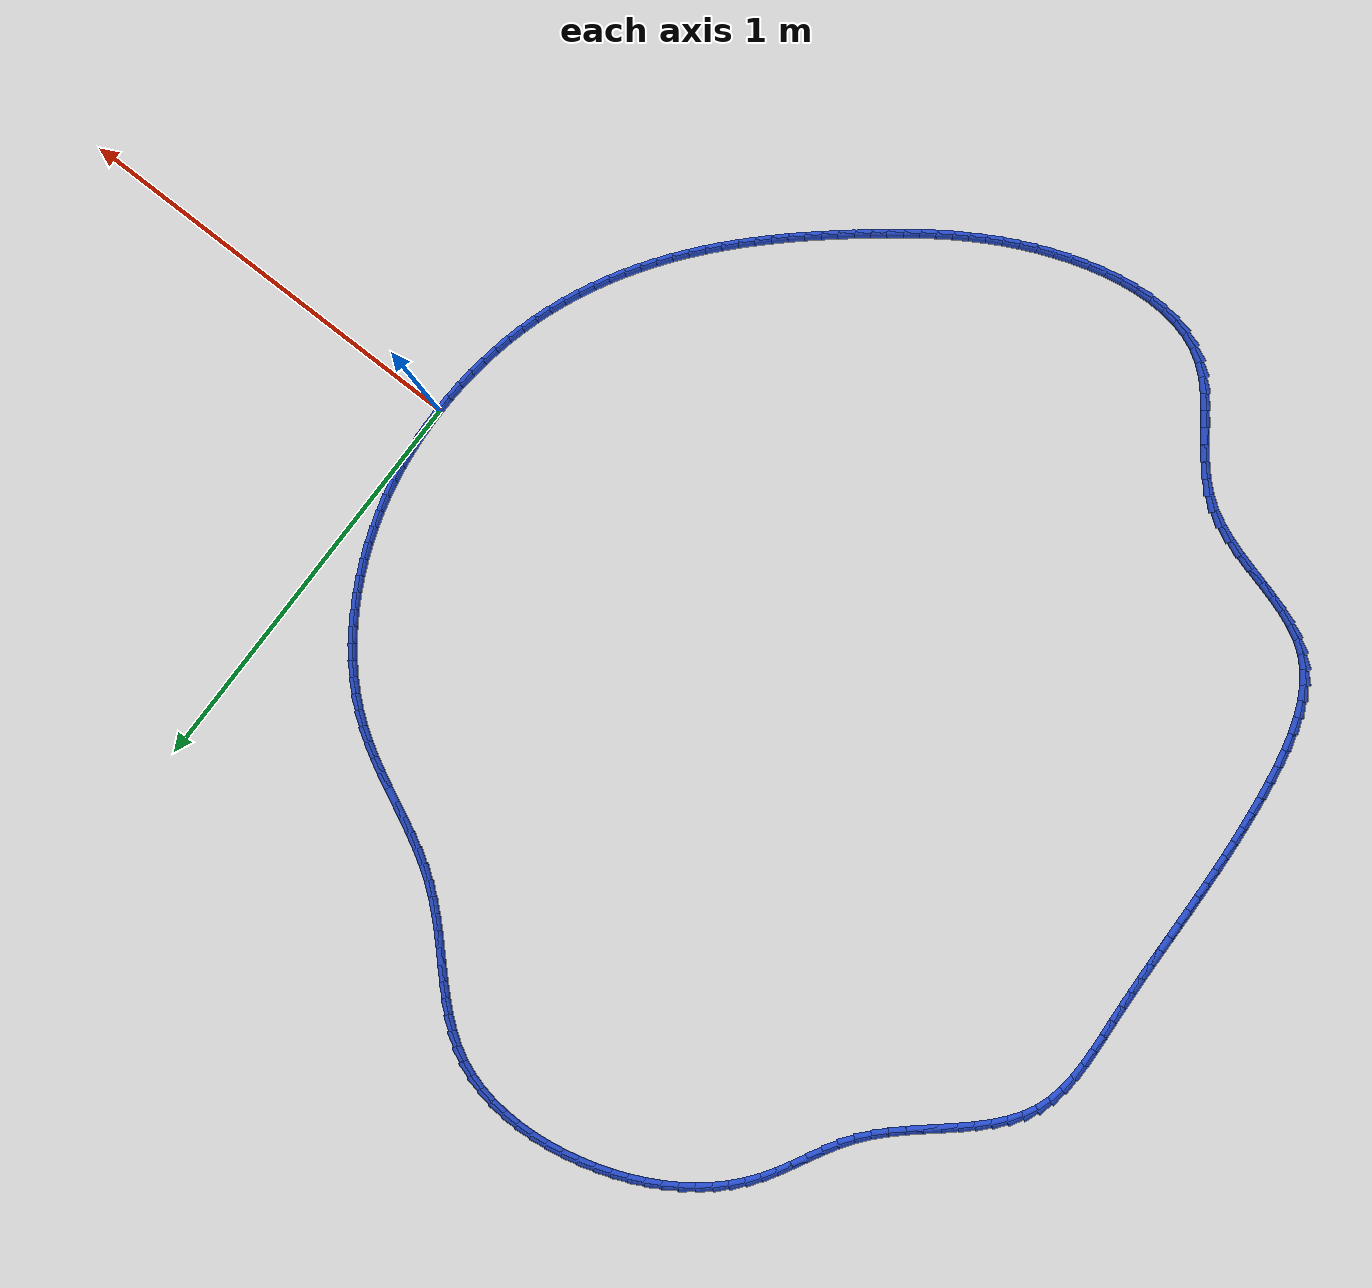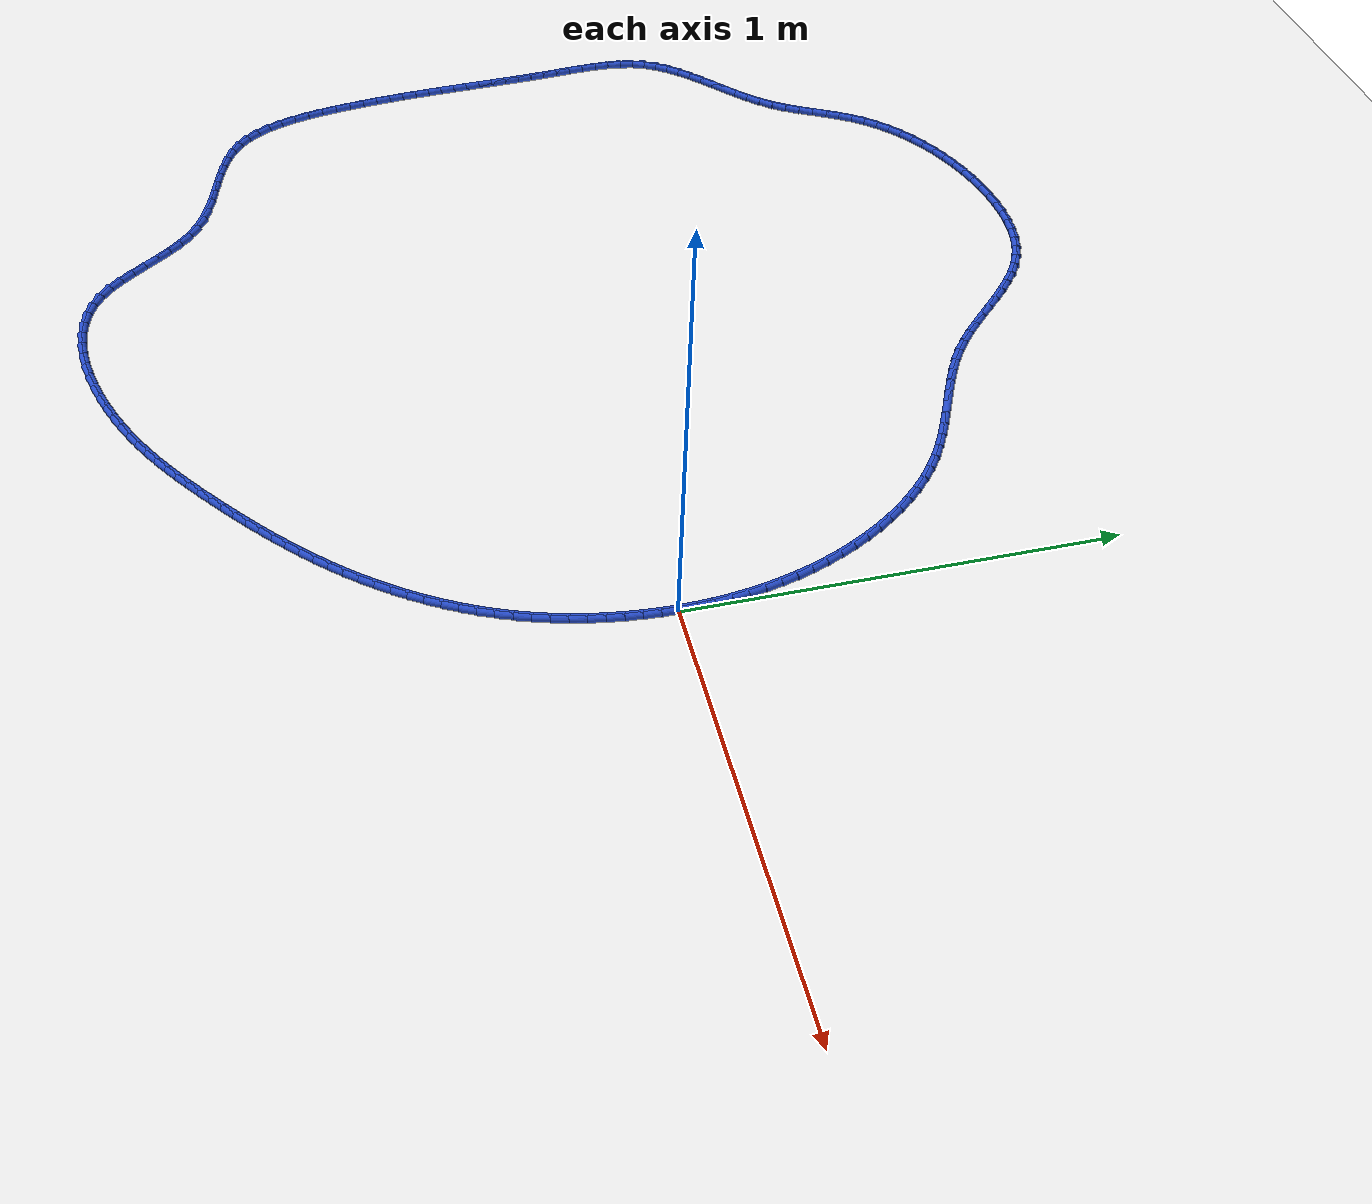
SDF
<sdf version="1.6">
 <world name="default">
  <light name="sun" type="directional">
   <pose>0 0 10 0 -0 0</pose>
   <diffuse>0.8 0.8 0.8 1</diffuse>
   <specular>0.2 0.2 0.2 1</specular>
   <attenuation>
    <range>1000</range>
    <constant>0.9</constant>
    <linear>0.01</linear>
    <quadratic>0.001</quadratic>
   </attenuation>
   <direction>-0.5 0.1 -0.9</direction>
  </light>
  <model name="ground_plane">
   <static>1</static>
   <link name="link">
    <collision name="collision">
     <geometry><plane><normal>0 0 1</normal><size>100 100</size></plane></geometry>
     <surface><friction><ode><mu>100</mu><mu2>50</mu2></ode></friction></surface>
    </collision>
    <visual name="visual">
     <cast_shadows>0</cast_shadows>
     <geometry><plane><normal>0 0 1</normal><size>100 100</size></plane></geometry>
     <material>
      <script><uri>file://media/materials/scripts/gazebo.material</uri><name>Gazebo/WhiteGlow</name></script>
     </material>
    </visual>
   </link>
  </model>
  <gravity>0 0 -9.8</gravity>
  <magnetic_field>6e-06 2.3e-05 -4.2e-05</magnetic_field>
  <atmosphere type="adiabatic"/>
  <physics name="default_physics" default="0" type="ode">
   <max_step_size>0.001</max_step_size>
   <real_time_factor>1</real_time_factor>
   <real_time_update_rate>1000</real_time_update_rate>
  </physics>
  <scene><ambient>0.4 0.4 0.4 1</ambient><background>0.7 0.7 0.7 1</background><shadows>1</shadows></scene>
  <spherical_coordinates>
   <surface_model>EARTH_WGS84</surface_model>
   <latitude_deg>0</latitude_deg>
   <longitude_deg>0</longitude_deg>
   <elevation>0</elevation>
   <heading_deg>0</heading_deg>
  </spherical_coordinates>
  <model name="line">
   <link name="link_0">
    <pose>1.5612511283791264e-17 4.85722573273506e-17 0.01 0 1.57 -1.555591541682877</pose>
    <collision name="collision">
     <geometry><cylinder><radius>0.01</radius><length>0.08</length></cylinder></geometry>
    </collision>
    <visual name="visual">
     <material>
      <script><name>Gazebo/Blue</name><uri>file://media/materials/scripts/gazebo.material</uri></script>
     </material>
     <geometry><cylinder><radius>0.01</radius><length>0.08</length></cylinder></geometry>
    </visual>
   </link>
   <link name="link_1">
    <pose>-0.0005885862749706142 0.0387076116104246 0.01 0 1.57 -1.5178129012271784</pose>
    <collision name="collision">
     <geometry><cylinder><radius>0.01</radius><length>0.08</length></cylinder></geometry>
    </collision>
    <visual name="visual">
     <material>
      <script><name>Gazebo/Blue</name><uri>file://media/materials/scripts/gazebo.material</uri></script>
     </material>
     <geometry><cylinder><radius>0.01</radius><length>0.08</length></cylinder></geometry>
    </visual>
   </link>
   <link name="link_2">
    <pose>-0.0026369221183866086 0.07733136492439875 0.01 0 1.57 -1.4791910282201761</pose>
    <collision name="collision">
     <geometry><cylinder><radius>0.01</radius><length>0.08</length></cylinder></geometry>
    </collision>
    <visual name="visual">
     <material>
      <script><name>Gazebo/Blue</name><uri>file://media/materials/scripts/gazebo.material</uri></script>
     </material>
     <geometry><cylinder><radius>0.01</radius><length>0.08</length></cylinder></geometry>
    </visual>
   </link>
   <link name="link_3">
    <pose>-0.006173445390191705 0.11582941587694119 0.01 0 1.57 -1.4397211803669223</pose>
    <collision name="collision">
     <geometry><cylinder><radius>0.01</radius><length>0.08</length></cylinder></geometry>
    </collision>
    <visual name="visual">
     <material>
      <script><name>Gazebo/Blue</name><uri>file://media/materials/scripts/gazebo.material</uri></script>
     </material>
     <geometry><cylinder><radius>0.01</radius><length>0.08</length></cylinder></geometry>
    </visual>
   </link>
   <link name="link_4">
    <pose>-0.011226593950329676 0.15415992040307078 0.01 0 1.57 -1.399408882495788</pose>
    <collision name="collision">
     <geometry><cylinder><radius>0.01</radius><length>0.08</length></cylinder></geometry>
    </collision>
    <visual name="visual">
     <material>
      <script><name>Gazebo/Blue</name><uri>file://media/materials/scripts/gazebo.material</uri></script>
     </material>
     <geometry><cylinder><radius>0.01</radius><length>0.08</length></cylinder></geometry>
    </visual>
   </link>
   <link name="link_5">
    <pose>-0.017824805658744253 0.1922810344378062 0.01 0 1.57 -1.3582709610619266</pose>
    <collision name="collision">
     <geometry><cylinder><radius>0.01</radius><length>0.08</length></cylinder></geometry>
    </collision>
    <visual name="visual">
     <material>
      <script><name>Gazebo/Blue</name><uri>file://media/materials/scripts/gazebo.material</uri></script>
     </material>
     <geometry><cylinder><radius>0.01</radius><length>0.08</length></cylinder></geometry>
    </visual>
   </link>
   <link name="link_6">
    <pose>-0.025996518375379217 0.23015091391616618 0.01 0 1.57 -1.3163364549275616</pose>
    <collision name="collision">
     <geometry><cylinder><radius>0.01</radius><length>0.08</length></cylinder></geometry>
    </collision>
    <visual name="visual">
     <material>
      <script><name>Gazebo/Blue</name><uri>file://media/materials/scripts/gazebo.material</uri></script>
     </material>
     <geometry><cylinder><radius>0.01</radius><length>0.08</length></cylinder></geometry>
    </visual>
   </link>
   <link name="link_7">
    <pose>-0.0357701699601783 0.26772771477316953 0.01 0 1.57 -1.2736473337954513</pose>
    <collision name="collision">
     <geometry><cylinder><radius>0.01</radius><length>0.08</length></cylinder></geometry>
    </collision>
    <visual name="visual">
     <material>
      <script><name>Gazebo/Blue</name><uri>file://media/materials/scripts/gazebo.material</uri></script>
     </material>
     <geometry><cylinder><radius>0.01</radius><length>0.08</length></cylinder></geometry>
    </visual>
   </link>
   <link name="link_8">
    <pose>-0.047174198273085284 0.3049695929438351 0.01 0 1.57 -1.2302589522736047</pose>
    <collision name="collision">
     <geometry><cylinder><radius>0.01</radius><length>0.08</length></cylinder></geometry>
    </collision>
    <visual name="visual">
     <material>
      <script><name>Gazebo/Blue</name><uri>file://media/materials/scripts/gazebo.material</uri></script>
     </material>
     <geometry><cylinder><radius>0.01</radius><length>0.08</length></cylinder></geometry>
    </visual>
   </link>
   <link name="link_9">
    <pose>-0.06023704117404391 0.34183470436318153 0.01 0 1.57 -1.186250848896145</pose>
    <collision name="collision">
     <geometry><cylinder><radius>0.01</radius><length>0.08</length></cylinder></geometry>
    </collision>
    <visual name="visual">
     <material>
      <script><name>Gazebo/Blue</name><uri>file://media/materials/scripts/gazebo.material</uri></script>
     </material>
     <geometry><cylinder><radius>0.01</radius><length>0.08</length></cylinder></geometry>
    </visual>
   </link>
   <link name="link_10">
    <pose>-0.07497886510807039 0.37826188552131335 0.01 0 1.57 -1.1415805041103357</pose>
    <collision name="collision">
     <geometry><cylinder><radius>0.01</radius><length>0.08</length></cylinder></geometry>
    </collision>
    <visual name="visual">
     <material>
      <script><name>Gazebo/Blue</name><uri>file://media/materials/scripts/gazebo.material</uri></script>
     </material>
     <geometry><cylinder><radius>0.01</radius><length>0.08</length></cylinder></geometry>
    </visual>
   </link>
   <link name="link_11">
    <pose>-0.0913862449718094 0.414111513530583 0.01 0 1.57 -1.0959408074885353</pose>
    <collision name="collision">
     <geometry><cylinder><radius>0.01</radius><length>0.08</length></cylinder></geometry>
    </collision>
    <visual name="visual">
     <material>
      <script><name>Gazebo/Blue</name><uri>file://media/materials/scripts/gazebo.material</uri></script>
     </material>
     <geometry><cylinder><radius>0.01</radius><length>0.08</length></cylinder></geometry>
    </visual>
   </link>
   <link name="link_12">
    <pose>-0.1094372293748518 0.44922405075665156 0.01 0 1.57 -1.0489952138966714</pose>
    <collision name="collision">
     <geometry><cylinder><radius>0.01</radius><length>0.08</length></cylinder></geometry>
    </collision>
    <visual name="visual">
     <material>
      <script><name>Gazebo/Blue</name><uri>file://media/materials/scripts/gazebo.material</uri></script>
     </material>
     <geometry><cylinder><radius>0.01</radius><length>0.08</length></cylinder></geometry>
    </visual>
   </link>
   <link name="link_13">
    <pose>-0.1291098669257019 0.4834399595626423 0.01 0 1.57 -1.000411944736257</pose>
    <collision name="collision">
     <geometry><cylinder><radius>0.01</radius><length>0.08</length></cylinder></geometry>
    </collision>
    <visual name="visual">
     <material>
      <script><name>Gazebo/Blue</name><uri>file://media/materials/scripts/gazebo.material</uri></script>
     </material>
     <geometry><cylinder><radius>0.01</radius><length>0.08</length></cylinder></geometry>
    </visual>
   </link>
   <link name="link_14">
    <pose>-0.15038220623286364 0.516599702311678 0.01 0 1.57 -0.94986480309257</pose>
    <collision name="collision">
     <geometry><cylinder><radius>0.01</radius><length>0.08</length></cylinder></geometry>
    </collision>
    <visual name="visual">
     <material>
      <script><name>Gazebo/Blue</name><uri>file://media/materials/scripts/gazebo.material</uri></script>
     </material>
     <geometry><cylinder><radius>0.01</radius><length>0.08</length></cylinder></geometry>
    </visual>
   </link>
   <link name="link_15">
    <pose>-0.17323229590484132 0.5485437413668817 0.01 0 1.57 -0.8970365400116441</pose>
    <collision name="collision">
     <geometry><cylinder><radius>0.01</radius><length>0.08</length></cylinder></geometry>
    </collision>
    <visual name="visual">
     <material>
      <script><name>Gazebo/Blue</name><uri>file://media/materials/scripts/gazebo.material</uri></script>
     </material>
     <geometry><cylinder><radius>0.01</radius><length>0.08</length></cylinder></geometry>
    </visual>
   </link>
   <link name="link_16">
    <pose>-0.1976381845501389 0.5791125390913763 0.01 0 1.57 -0.8416253755599946</pose>
    <collision name="collision">
     <geometry><cylinder><radius>0.01</radius><length>0.08</length></cylinder></geometry>
    </collision>
    <visual name="visual">
     <material>
      <script><name>Gazebo/Blue</name><uri>file://media/materials/scripts/gazebo.material</uri></script>
     </material>
     <geometry><cylinder><radius>0.01</radius><length>0.08</length></cylinder></geometry>
    </visual>
   </link>
   <link name="link_17">
    <pose>-0.22357792077726069 0.6081465578482849 0.01 0 1.57 -0.7833553201234023</pose>
    <collision name="collision">
     <geometry><cylinder><radius>0.01</radius><length>0.08</length></cylinder></geometry>
    </collision>
    <visual name="visual">
     <material>
      <script><name>Gazebo/Blue</name><uri>file://media/materials/scripts/gazebo.material</uri></script>
     </material>
     <geometry><cylinder><radius>0.01</radius><length>0.08</length></cylinder></geometry>
    </visual>
   </link>
   <link name="link_18">
    <pose>-0.2510295531947108 0.63548626000073 0.01 0 1.57 -0.721990849593027</pose>
    <collision name="collision">
     <geometry><cylinder><radius>0.01</radius><length>0.08</length></cylinder></geometry>
    </collision>
    <visual name="visual">
     <material>
      <script><name>Gazebo/Blue</name><uri>file://media/materials/scripts/gazebo.material</uri></script>
     </material>
     <geometry><cylinder><radius>0.01</radius><length>0.08</length></cylinder></geometry>
    </visual>
   </link>
   <link name="link_19">
    <pose>-0.27997113041099336 0.6609721079118354 0.01 0 1.57 -0.6573561689004592</pose>
    <collision name="collision">
     <geometry><cylinder><radius>0.01</radius><length>0.08</length></cylinder></geometry>
    </collision>
    <visual name="visual">
     <material>
      <script><name>Gazebo/Blue</name><uri>file://media/materials/scripts/gazebo.material</uri></script>
     </material>
     <geometry><cylinder><radius>0.01</radius><length>0.08</length></cylinder></geometry>
    </visual>
   </link>
   <link name="link_20">
    <pose>-0.3103807009848645 0.6844445640585316 0.01 0 1.57 -0.5922400379620084</pose>
    <collision name="collision">
     <geometry><cylinder><radius>0.01</radius><length>0.08</length></cylinder></geometry>
    </collision>
    <visual name="visual">
     <material>
      <script><name>Gazebo/Blue</name><uri>file://media/materials/scripts/gazebo.material</uri></script>
     </material>
     <geometry><cylinder><radius>0.01</radius><length>0.08</length></cylinder></geometry>
    </visual>
   </link>
   <link name="link_21">
    <pose>-0.3421913610556993 0.7058469282699311 0.01 0 1.57 -0.5380046331219901</pose>
    <collision name="collision">
     <geometry><cylinder><radius>0.01</radius><length>0.08</length></cylinder></geometry>
    </collision>
    <visual name="visual">
     <material>
      <script><name>Gazebo/Blue</name><uri>file://media/materials/scripts/gazebo.material</uri></script>
     </material>
     <geometry><cylinder><radius>0.01</radius><length>0.08</length></cylinder></geometry>
    </visual>
   </link>
   <link name="link_22">
    <pose>-0.37516194686955634 0.725521153579287 0.01 0 1.57 -0.497581631554111</pose>
    <collision name="collision">
     <geometry><cylinder><radius>0.01</radius><length>0.08</length></cylinder></geometry>
    </collision>
    <visual name="visual">
     <material>
      <script><name>Gazebo/Blue</name><uri>file://media/materials/scripts/gazebo.material</uri></script>
     </material>
     <geometry><cylinder><radius>0.01</radius><length>0.08</length></cylinder></geometry>
    </visual>
   </link>
   <link name="link_23">
    <pose>-0.40900907458085145 0.7439057796439568 0.01 0 1.57 -0.4709014705955147</pose>
    <collision name="collision">
     <geometry><cylinder><radius>0.01</radius><length>0.08</length></cylinder></geometry>
    </collision>
    <visual name="visual">
     <material>
      <script><name>Gazebo/Blue</name><uri>file://media/materials/scripts/gazebo.material</uri></script>
     </material>
     <geometry><cylinder><radius>0.01</radius><length>0.08</length></cylinder></geometry>
    </visual>
   </link>
   <link name="link_24">
    <pose>-0.4434493603440008 0.7614393461212969 0.01 0 1.57 -0.4577834412397186</pose>
    <collision name="collision">
     <geometry><cylinder><radius>0.01</radius><length>0.08</length></cylinder></geometry>
    </collision>
    <visual name="visual">
     <material>
      <script><name>Gazebo/Blue</name><uri>file://media/materials/scripts/gazebo.material</uri></script>
     </material>
     <geometry><cylinder><radius>0.01</radius><length>0.08</length></cylinder></geometry>
    </visual>
   </link>
   <link name="link_25">
    <pose>-0.47819942031342094 0.7785603926686655 0.01 0 1.57 -0.4580845987460513</pose>
    <collision name="collision">
     <geometry><cylinder><radius>0.01</radius><length>0.08</length></cylinder></geometry>
    </collision>
    <visual name="visual">
     <material>
      <script><name>Gazebo/Blue</name><uri>file://media/materials/scripts/gazebo.material</uri></script>
     </material>
     <geometry><cylinder><radius>0.01</radius><length>0.08</length></cylinder></geometry>
    </visual>
   </link>
   <link name="link_26">
    <pose>-0.5129758706435278 0.7957074589434193 0.01 0 1.57 -0.47176964728399934</pose>
    <collision name="collision">
     <geometry><cylinder><radius>0.01</radius><length>0.08</length></cylinder></geometry>
    </collision>
    <visual name="visual">
     <material>
      <script><name>Gazebo/Blue</name><uri>file://media/materials/scripts/gazebo.material</uri></script>
     </material>
     <geometry><cylinder><radius>0.01</radius><length>0.08</length></cylinder></geometry>
    </visual>
   </link>
   <link name="link_27">
    <pose>-0.5474953274887373 0.8133190846029155 0.01 0 1.57 -0.49890843818367014</pose>
    <collision name="collision">
     <geometry><cylinder><radius>0.01</radius><length>0.08</length></cylinder></geometry>
    </collision>
    <visual name="visual">
     <material>
      <script><name>Gazebo/Blue</name><uri>file://media/materials/scripts/gazebo.material</uri></script>
     </material>
     <geometry><cylinder><radius>0.01</radius><length>0.08</length></cylinder></geometry>
    </visual>
   </link>
   <link name="link_28">
    <pose>-0.5814744070034661 0.8318338093045117 0.01 0 1.57 -0.5396023647115948</pose>
    <collision name="collision">
     <geometry><cylinder><radius>0.01</radius><length>0.08</length></cylinder></geometry>
    </collision>
    <visual name="visual">
     <material>
      <script><name>Gazebo/Blue</name><uri>file://media/materials/scripts/gazebo.material</uri></script>
     </material>
     <geometry><cylinder><radius>0.01</radius><length>0.08</length></cylinder></geometry>
    </visual>
   </link>
   <link name="link_29">
    <pose>-0.6146297253421301 0.8516901727055649 0.01 0 1.57 -0.5938359373206173</pose>
    <collision name="collision">
     <geometry><cylinder><radius>0.01</radius><length>0.08</length></cylinder></geometry>
    </collision>
    <visual name="visual">
     <material>
      <script><name>Gazebo/Blue</name><uri>file://media/materials/scripts/gazebo.material</uri></script>
     </material>
     <geometry><cylinder><radius>0.01</radius><length>0.08</length></cylinder></geometry>
    </visual>
   </link>
   <link name="link_30">
    <pose>-0.6466778986591456 0.8733267144634322 0.01 0 1.57 -0.6600343421150673</pose>
    <collision name="collision">
     <geometry><cylinder><radius>0.01</radius><length>0.08</length></cylinder></geometry>
    </collision>
    <visual name="visual">
     <material>
      <script><name>Gazebo/Blue</name><uri>file://media/materials/scripts/gazebo.material</uri></script>
     </material>
     <geometry><cylinder><radius>0.01</radius><length>0.08</length></cylinder></geometry>
    </visual>
   </link>
   <link name="link_31">
    <pose>-0.6773601640706979 0.8971410598061532 0.01 0 1.57 -0.7209493918232626</pose>
    <collision name="collision">
     <geometry><cylinder><radius>0.01</radius><length>0.08</length></cylinder></geometry>
    </collision>
    <visual name="visual">
     <material>
      <script><name>Gazebo/Blue</name><uri>file://media/materials/scripts/gazebo.material</uri></script>
     </material>
     <geometry><cylinder><radius>0.01</radius><length>0.08</length></cylinder></geometry>
    </visual>
   </link>
   <link name="link_32">
    <pose>-0.7067544776524084 0.9229712837624436 0.01 0 1.57 -0.7647690480422902</pose>
    <collision name="collision">
     <geometry><cylinder><radius>0.01</radius><length>0.08</length></cylinder></geometry>
    </collision>
    <visual name="visual">
     <material>
      <script><name>Gazebo/Blue</name><uri>file://media/materials/scripts/gazebo.material</uri></script>
     </material>
     <geometry><cylinder><radius>0.01</radius><length>0.08</length></cylinder></geometry>
    </visual>
   </link>
   <link name="link_33">
    <pose>-0.7351826971803456 0.9502501523005189 0.01 0 1.57 -0.7918654375088664</pose>
    <collision name="collision">
     <geometry><cylinder><radius>0.01</radius><length>0.08</length></cylinder></geometry>
    </collision>
    <visual name="visual">
     <material>
      <script><name>Gazebo/Blue</name><uri>file://media/materials/scripts/gazebo.material</uri></script>
     </material>
     <geometry><cylinder><radius>0.01</radius><length>0.08</length></cylinder></geometry>
    </visual>
   </link>
   <link name="link_34">
    <pose>-0.7629721306492725 0.978401374366791 0.01 0 1.57 -0.8027290159153724</pose>
    <collision name="collision">
     <geometry><cylinder><radius>0.01</radius><length>0.08</length></cylinder></geometry>
    </collision>
    <visual name="visual">
     <material>
      <script><name>Gazebo/Blue</name><uri>file://media/materials/scripts/gazebo.material</uri></script>
     </material>
     <geometry><cylinder><radius>0.01</radius><length>0.08</length></cylinder></geometry>
    </visual>
   </link>
   <link name="link_35">
    <pose>-0.7904500860539536 1.0068486589076735 0.01 0 1.57 -0.7974935212478353</pose>
    <collision name="collision">
     <geometry><cylinder><radius>0.01</radius><length>0.08</length></cylinder></geometry>
    </collision>
    <visual name="visual">
     <material>
      <script><name>Gazebo/Blue</name><uri>file://media/materials/scripts/gazebo.material</uri></script>
     </material>
     <geometry><cylinder><radius>0.01</radius><length>0.08</length></cylinder></geometry>
    </visual>
   </link>
   <link name="link_36">
    <pose>-0.8179438713891519 1.035015714869578 0.01 0 1.57 -0.7758533729427121</pose>
    <collision name="collision">
     <geometry><cylinder><radius>0.01</radius><length>0.08</length></cylinder></geometry>
    </collision>
    <visual name="visual">
     <material>
      <script><name>Gazebo/Blue</name><uri>file://media/materials/scripts/gazebo.material</uri></script>
     </material>
     <geometry><cylinder><radius>0.01</radius><length>0.08</length></cylinder></geometry>
    </visual>
   </link>
   <link name="link_37">
    <pose>-0.8457807946496312 1.062326251198917 0.01 0 1.57 -0.7370835084984296</pose>
    <collision name="collision">
     <geometry><cylinder><radius>0.01</radius><length>0.08</length></cylinder></geometry>
    </collision>
    <visual name="visual">
     <material>
      <script><name>Gazebo/Blue</name><uri>file://media/materials/scripts/gazebo.material</uri></script>
     </material>
     <geometry><cylinder><radius>0.01</radius><length>0.08</length></cylinder></geometry>
    </visual>
   </link>
   <link name="link_38">
    <pose>-0.8742881638301547 1.0882039768421035 0.01 0 1.57 -0.6801837960113646</pose>
    <collision name="collision">
     <geometry><cylinder><radius>0.01</radius><length>0.08</length></cylinder></geometry>
    </collision>
    <visual name="visual">
     <material>
      <script><name>Gazebo/Blue</name><uri>file://media/materials/scripts/gazebo.material</uri></script>
     </material>
     <geometry><cylinder><radius>0.01</radius><length>0.08</length></cylinder></geometry>
    </visual>
   </link>
   <link name="link_39">
    <pose>-0.9037932869254865 1.11207260074555 0.01 0 1.57 -0.6042115472105837</pose>
    <collision name="collision">
     <geometry><cylinder><radius>0.01</radius><length>0.08</length></cylinder></geometry>
    </collision>
    <visual name="visual">
     <material>
      <script><name>Gazebo/Blue</name><uri>file://media/materials/scripts/gazebo.material</uri></script>
     </material>
     <geometry><cylinder><radius>0.01</radius><length>0.08</length></cylinder></geometry>
    </visual>
   </link>
   <link name="link_40">
    <pose>-0.9346234719303901 1.133355831855668 0.01 0 1.57 -0.5088771930069838</pose>
    <collision name="collision">
     <geometry><cylinder><radius>0.01</radius><length>0.08</length></cylinder></geometry>
    </collision>
    <visual name="visual">
     <material>
      <script><name>Gazebo/Blue</name><uri>file://media/materials/scripts/gazebo.material</uri></script>
     </material>
     <geometry><cylinder><radius>0.01</radius><length>0.08</length></cylinder></geometry>
    </visual>
   </link>
   <link name="link_41">
    <pose>-0.9671060268396291 1.1514773791188715 0.01 0 1.57 -0.3993842038170686</pose>
    <collision name="collision">
     <geometry><cylinder><radius>0.01</radius><length>0.08</length></cylinder></geometry>
    </collision>
    <visual name="visual">
     <material>
      <script><name>Gazebo/Blue</name><uri>file://media/materials/scripts/gazebo.material</uri></script>
     </material>
     <geometry><cylinder><radius>0.01</radius><length>0.08</length></cylinder></geometry>
    </visual>
   </link>
   <link name="link_42">
    <pose>-1.0014712898155775 1.165981840963148 0.01 0 1.57 -0.29454954107456244</pose>
    <collision name="collision">
     <geometry><cylinder><radius>0.01</radius><length>0.08</length></cylinder></geometry>
    </collision>
    <visual name="visual">
     <material>
      <script><name>Gazebo/Blue</name><uri>file://media/materials/scripts/gazebo.material</uri></script>
     </material>
     <geometry><cylinder><radius>0.01</radius><length>0.08</length></cylinder></geometry>
    </visual>
   </link>
   <link name="link_43">
    <pose>-1.0375401888467142 1.17692421562285 0.01 0 1.57 -0.19926425194213804</pose>
    <collision name="collision">
     <geometry><cylinder><radius>0.01</radius><length>0.08</length></cylinder></geometry>
    </collision>
    <visual name="visual">
     <material>
      <script><name>Gazebo/Blue</name><uri>file://media/materials/scripts/gazebo.material</uri></script>
     </material>
     <geometry><cylinder><radius>0.01</radius><length>0.08</length></cylinder></geometry>
    </visual>
   </link>
   <link name="link_44">
    <pose>-1.075025621205614 1.1844941800970346 0.01 0 1.57 -0.11313000391877812</pose>
    <collision name="collision">
     <geometry><cylinder><radius>0.01</radius><length>0.08</length></cylinder></geometry>
    </collision>
    <visual name="visual">
     <material>
      <script><name>Gazebo/Blue</name><uri>file://media/materials/scripts/gazebo.material</uri></script>
     </material>
     <geometry><cylinder><radius>0.01</radius><length>0.08</length></cylinder></geometry>
    </visual>
   </link>
   <link name="link_45">
    <pose>-1.1136404835672107 1.1888814121298201 0.01 0 1.57 -0.035319230790393445</pose>
    <collision name="collision">
     <geometry><cylinder><radius>0.01</radius><length>0.08</length></cylinder></geometry>
    </collision>
    <visual name="visual">
     <material>
      <script><name>Gazebo/Blue</name><uri>file://media/materials/scripts/gazebo.material</uri></script>
     </material>
     <geometry><cylinder><radius>0.01</radius><length>0.08</length></cylinder></geometry>
    </visual>
   </link>
   <link name="link_46">
    <pose>-1.1530976726064388 1.1902755894653265 0.01 0 1.57 0.035204510748973315</pose>
    <collision name="collision">
     <geometry><cylinder><radius>0.01</radius><length>0.08</length></cylinder></geometry>
    </collision>
    <visual name="visual">
     <material>
      <script><name>Gazebo/Blue</name><uri>file://media/materials/scripts/gazebo.material</uri></script>
     </material>
     <geometry><cylinder><radius>0.01</radius><length>0.08</length></cylinder></geometry>
    </visual>
   </link>
   <link name="link_47">
    <pose>-1.193110084998232 1.1888663898476728 0.01 0 1.57 0.0995419549093709</pose>
    <collision name="collision">
     <geometry><cylinder><radius>0.01</radius><length>0.08</length></cylinder></geometry>
    </collision>
    <visual name="visual">
     <material>
      <script><name>Gazebo/Blue</name><uri>file://media/materials/scripts/gazebo.material</uri></script>
     </material>
     <geometry><cylinder><radius>0.01</radius><length>0.08</length></cylinder></geometry>
    </visual>
   </link>
   <link name="link_48">
    <pose>-1.2333906174175235 1.1848434910209773 0.01 0 1.57 0.15877810201861178</pose>
    <collision name="collision">
     <geometry><cylinder><radius>0.01</radius><length>0.08</length></cylinder></geometry>
    </collision>
    <visual name="visual">
     <material>
      <script><name>Gazebo/Blue</name><uri>file://media/materials/scripts/gazebo.material</uri></script>
     </material>
     <geometry><cylinder><radius>0.01</radius><length>0.08</length></cylinder></geometry>
    </visual>
   </link>
   <link name="link_49">
    <pose>-1.2736521665392488 1.17839657072936 0.01 0 1.57 0.2139482124098432</pose>
    <collision name="collision">
     <geometry><cylinder><radius>0.01</radius><length>0.08</length></cylinder></geometry>
    </collision>
    <visual name="visual">
     <material>
      <script><name>Gazebo/Blue</name><uri>file://media/materials/scripts/gazebo.material</uri></script>
     </material>
     <geometry><cylinder><radius>0.01</radius><length>0.08</length></cylinder></geometry>
    </visual>
   </link>
   <link name="link_50">
    <pose>-1.31360762903834 1.1697153067169397 0.01 0 1.57 0.26650997834012896</pose>
    <collision name="collision">
     <geometry><cylinder><radius>0.01</radius><length>0.08</length></cylinder></geometry>
    </collision>
    <visual name="visual">
     <material>
      <script><name>Gazebo/Blue</name><uri>file://media/materials/scripts/gazebo.material</uri></script>
     </material>
     <geometry><cylinder><radius>0.01</radius><length>0.08</length></cylinder></geometry>
    </visual>
   </link>
   <link name="link_51">
    <pose>-1.3529826562256022 1.1589657507992683 0.01 0 1.57 0.31961463470445206</pose>
    <collision name="collision">
     <geometry><cylinder><radius>0.01</radius><length>0.08</length></cylinder></geometry>
    </collision>
    <visual name="visual">
     <material>
      <script><name>Gazebo/Blue</name><uri>file://media/materials/scripts/gazebo.material</uri></script>
     </material>
     <geometry><cylinder><radius>0.01</radius><length>0.08</length></cylinder></geometry>
    </visual>
   </link>
   <link name="link_52">
    <pose>-1.3915666126840012 1.1461959361175709 0.01 0 1.57 0.3744847786997875</pose>
    <collision name="collision">
     <geometry><cylinder><radius>0.01</radius><length>0.08</length></cylinder></geometry>
    </collision>
    <visual name="visual">
     <material>
      <script><name>Gazebo/Blue</name><uri>file://media/materials/scripts/gazebo.material</uri></script>
     </material>
     <geometry><cylinder><radius>0.01</radius><length>0.08</length></cylinder></geometry>
    </visual>
   </link>
   <link name="link_53">
    <pose>-1.4291687171838194 1.1314171190978346 0.01 0 1.57 0.43156946655705075</pose>
    <collision name="collision">
     <geometry><cylinder><radius>0.01</radius><length>0.08</length></cylinder></geometry>
    </collision>
    <visual name="visual">
     <material>
      <script><name>Gazebo/Blue</name><uri>file://media/materials/scripts/gazebo.material</uri></script>
     </material>
     <geometry><cylinder><radius>0.01</radius><length>0.08</length></cylinder></geometry>
    </visual>
   </link>
   <link name="link_54">
    <pose>-1.4655981949578503 1.11464054419528 0.01 0 1.57 0.4913146990866038</pose>
    <collision name="collision">
     <geometry><cylinder><radius>0.01</radius><length>0.08</length></cylinder></geometry>
    </collision>
    <visual name="visual">
     <material>
      <script><name>Gazebo/Blue</name><uri>file://media/materials/scripts/gazebo.material</uri></script>
     </material>
     <geometry><cylinder><radius>0.01</radius><length>0.08</length></cylinder></geometry>
    </visual>
   </link>
   <link name="link_55">
    <pose>-1.5006642712388876 1.0958774558651274 0.01 0 1.57 0.5541542140938653</pose>
    <collision name="collision">
     <geometry><cylinder><radius>0.01</radius><length>0.08</length></cylinder></geometry>
    </collision>
    <visual name="visual">
     <material>
      <script><name>Gazebo/Blue</name><uri>file://media/materials/scripts/gazebo.material</uri></script>
     </material>
     <geometry><cylinder><radius>0.01</radius><length>0.08</length></cylinder></geometry>
    </visual>
   </link>
   <link name="link_56">
    <pose>-1.5341761712597228 1.0751390985625968 0.01 0 1.57 0.6204934053421207</pose>
    <collision name="collision">
     <geometry><cylinder><radius>0.01</radius><length>0.08</length></cylinder></geometry>
    </collision>
    <visual name="visual">
     <material>
      <script><name>Gazebo/Blue</name><uri>file://media/materials/scripts/gazebo.material</uri></script>
     </material>
     <geometry><cylinder><radius>0.01</radius><length>0.08</length></cylinder></geometry>
    </visual>
   </link>
   <link name="link_57">
    <pose>-1.56594312025315 1.0524367167429085 0.01 0 1.57 0.6906850596506369</pose>
    <collision name="collision">
     <geometry><cylinder><radius>0.01</radius><length>0.08</length></cylinder></geometry>
    </collision>
    <visual name="visual">
     <material>
      <script><name>Gazebo/Blue</name><uri>file://media/materials/scripts/gazebo.material</uri></script>
     </material>
     <geometry><cylinder><radius>0.01</radius><length>0.08</length></cylinder></geometry>
    </visual>
   </link>
   <link name="link_58">
    <pose>-1.5957743434519618 1.027781554861283 0.01 0 1.57 0.7649959086756521</pose>
    <collision name="collision">
     <geometry><cylinder><radius>0.01</radius><length>0.08</length></cylinder></geometry>
    </collision>
    <visual name="visual">
     <material>
      <script><name>Gazebo/Blue</name><uri>file://media/materials/scripts/gazebo.material</uri></script>
     </material>
     <geometry><cylinder><radius>0.01</radius><length>0.08</length></cylinder></geometry>
    </visual>
   </link>
   <link name="link_59">
    <pose>-1.6234790660889502 1.0011848573729405 0.01 0 1.57 0.8435644002538337</pose>
    <collision name="collision">
     <geometry><cylinder><radius>0.01</radius><length>0.08</length></cylinder></geometry>
    </collision>
    <visual name="visual">
     <material>
      <script><name>Gazebo/Blue</name><uri>file://media/materials/scripts/gazebo.material</uri></script>
     </material>
     <geometry><cylinder><radius>0.01</radius><length>0.08</length></cylinder></geometry>
    </visual>
   </link>
   <link name="link_60">
    <pose>-1.6488665133969096 0.9726578687331009 0.01 0 1.57 0.9263526668702404</pose>
    <collision name="collision">
     <geometry><cylinder><radius>0.01</radius><length>0.08</length></cylinder></geometry>
    </collision>
    <visual name="visual">
     <material>
      <script><name>Gazebo/Blue</name><uri>file://media/materials/scripts/gazebo.material</uri></script>
     </material>
     <geometry><cylinder><radius>0.01</radius><length>0.08</length></cylinder></geometry>
    </visual>
   </link>
   <link name="link_61">
    <pose>-1.6717459106086312 0.9422118333969852 0.01 0 1.57 1.0075000632424655</pose>
    <collision name="collision">
     <geometry><cylinder><radius>0.01</radius><length>0.08</length></cylinder></geometry>
    </collision>
    <visual name="visual">
     <material>
      <script><name>Gazebo/Blue</name><uri>file://media/materials/scripts/gazebo.material</uri></script>
     </material>
     <geometry><cylinder><radius>0.01</radius><length>0.08</length></cylinder></geometry>
    </visual>
   </link>
   <link name="link_62">
    <pose>-1.6921159861635364 0.9099577851358764 0.01 0 1.57 1.0634153610228012</pose>
    <collision name="collision">
     <geometry><cylinder><radius>0.01</radius><length>0.08</length></cylinder></geometry>
    </collision>
    <visual name="visual">
     <material>
      <script><name>Gazebo/Blue</name><uri>file://media/materials/scripts/gazebo.material</uri></script>
     </material>
     <geometry><cylinder><radius>0.01</radius><length>0.08</length></cylinder></geometry>
    </visual>
   </link>
   <link name="link_63">
    <pose>-1.71076042932323 0.876420105362906 0.01 0 1.57 1.0883585617829186</pose>
    <collision name="collision">
     <geometry><cylinder><radius>0.01</radius><length>0.08</length></cylinder></geometry>
    </collision>
    <visual name="visual">
     <material>
      <script><name>Gazebo/Blue</name><uri>file://media/materials/scripts/gazebo.material</uri></script>
     </material>
     <geometry><cylinder><radius>0.01</radius><length>0.08</length></cylinder></geometry>
    </visual>
   </link>
   <link name="link_64">
    <pose>-1.728666144341941 0.8422301852114578 0.01 0 1.57 1.0829316426552231</pose>
    <collision name="collision">
     <geometry><cylinder><radius>0.01</radius><length>0.08</length></cylinder></geometry>
    </collision>
    <visual name="visual">
     <material>
      <script><name>Gazebo/Blue</name><uri>file://media/materials/scripts/gazebo.material</uri></script>
     </material>
     <geometry><cylinder><radius>0.01</radius><length>0.08</length></cylinder></geometry>
    </visual>
   </link>
   <link name="link_65">
    <pose>-1.7468200357837422 0.8080194159780715 0.01 0 1.57 1.0474236435754225</pose>
    <collision name="collision">
     <geometry><cylinder><radius>0.01</radius><length>0.08</length></cylinder></geometry>
    </collision>
    <visual name="visual">
     <material>
      <script><name>Gazebo/Blue</name><uri>file://media/materials/scripts/gazebo.material</uri></script>
     </material>
     <geometry><cylinder><radius>0.01</radius><length>0.08</length></cylinder></geometry>
    </visual>
   </link>
   <link name="link_66">
    <pose>-1.7662090082127027 0.774419188959286 0.01 0 1.57 0.9819648597125538</pose>
    <collision name="collision">
     <geometry><cylinder><radius>0.01</radius><length>0.08</length></cylinder></geometry>
    </collision>
    <visual name="visual">
     <material>
      <script><name>Gazebo/Blue</name><uri>file://media/materials/scripts/gazebo.material</uri></script>
     </material>
     <geometry><cylinder><radius>0.01</radius><length>0.08</length></cylinder></geometry>
    </visual>
   </link>
   <link name="link_67">
    <pose>-1.7878199661928926 0.7420608954516416 0.01 0 1.57 0.894094415736364</pose>
    <collision name="collision">
     <geometry><cylinder><radius>0.01</radius><length>0.08</length></cylinder></geometry>
    </collision>
    <visual name="visual">
     <material>
      <script><name>Gazebo/Blue</name><uri>file://media/materials/scripts/gazebo.material</uri></script>
     </material>
     <geometry><cylinder><radius>0.01</radius><length>0.08</length></cylinder></geometry>
    </visual>
   </link>
   <link name="link_68">
    <pose>-1.812412441832844 0.7114435756504468 0.01 0 1.57 0.8183840238640808</pose>
    <collision name="collision">
     <geometry><cylinder><radius>0.01</radius><length>0.08</length></cylinder></geometry>
    </collision>
    <visual name="visual">
     <material>
      <script><name>Gazebo/Blue</name><uri>file://media/materials/scripts/gazebo.material</uri></script>
     </material>
     <geometry><cylinder><radius>0.01</radius><length>0.08</length></cylinder></geometry>
    </visual>
   </link>
   <link name="link_69">
    <pose>-1.839600796966233 0.6823996782475864 0.01 0 1.57 0.7644568316218366</pose>
    <collision name="collision">
     <geometry><cylinder><radius>0.01</radius><length>0.08</length></cylinder></geometry>
    </collision>
    <visual name="visual">
     <material>
      <script><name>Gazebo/Blue</name><uri>file://media/materials/scripts/gazebo.material</uri></script>
     </material>
     <geometry><cylinder><radius>0.01</radius><length>0.08</length></cylinder></geometry>
    </visual>
   </link>
   <link name="link_70">
    <pose>-1.8686396657638569 0.6545522582675709 0.01 0 1.57 0.7309510090940847</pose>
    <collision name="collision">
     <geometry><cylinder><radius>0.01</radius><length>0.08</length></cylinder></geometry>
    </collision>
    <visual name="visual">
     <material>
      <script><name>Gazebo/Blue</name><uri>file://media/materials/scripts/gazebo.material</uri></script>
     </material>
     <geometry><cylinder><radius>0.01</radius><length>0.08</length></cylinder></geometry>
    </visual>
   </link>
   <link name="link_71">
    <pose>-1.8987835528806638 0.6275242953451042 0.01 0 1.57 0.7168778744353141</pose>
    <collision name="collision">
     <geometry><cylinder><radius>0.01</radius><length>0.08</length></cylinder></geometry>
    </collision>
    <visual name="visual">
     <material>
      <script><name>Gazebo/Blue</name><uri>file://media/materials/scripts/gazebo.material</uri></script>
     </material>
     <geometry><cylinder><radius>0.01</radius><length>0.08</length></cylinder></geometry>
    </visual>
   </link>
   <link name="link_72">
    <pose>-1.929286962971602 0.6009387691148912 0.01 0 1.57 0.7219684729193467</pose>
    <collision name="collision">
     <geometry><cylinder><radius>0.01</radius><length>0.08</length></cylinder></geometry>
    </collision>
    <visual name="visual">
     <material>
      <script><name>Gazebo/Blue</name><uri>file://media/materials/scripts/gazebo.material</uri></script>
     </material>
     <geometry><cylinder><radius>0.01</radius><length>0.08</length></cylinder></geometry>
    </visual>
   </link>
   <link name="link_73">
    <pose>-1.9594044006916203 0.5744186592116359 0.01 0 1.57 0.7468228006962894</pose>
    <collision name="collision">
     <geometry><cylinder><radius>0.01</radius><length>0.08</length></cylinder></geometry>
    </collision>
    <visual name="visual">
     <material>
      <script><name>Gazebo/Blue</name><uri>file://media/materials/scripts/gazebo.material</uri></script>
     </material>
     <geometry><cylinder><radius>0.01</radius><length>0.08</length></cylinder></geometry>
    </visual>
   </link>
   <link name="link_74">
    <pose>-1.988390370695667 0.5475869452700428 0.01 0 1.57 0.7929275164777811</pose>
    <collision name="collision">
     <geometry><cylinder><radius>0.01</radius><length>0.08</length></cylinder></geometry>
    </collision>
    <visual name="visual">
     <material>
      <script><name>Gazebo/Blue</name><uri>file://media/materials/scripts/gazebo.material</uri></script>
     </material>
     <geometry><cylinder><radius>0.01</radius><length>0.08</length></cylinder></geometry>
    </visual>
   </link>
   <link name="link_75">
    <pose>-2.0154993776386902 0.5200666069248163 0.01 0 1.57 0.8624872080030023</pose>
    <collision name="collision">
     <geometry><cylinder><radius>0.01</radius><length>0.08</length></cylinder></geometry>
    </collision>
    <visual name="visual">
     <material>
      <script><name>Gazebo/Blue</name><uri>file://media/materials/scripts/gazebo.material</uri></script>
     </material>
     <geometry><cylinder><radius>0.01</radius><length>0.08</length></cylinder></geometry>
    </visual>
   </link>
   <link name="link_76">
    <pose>-2.039985926175638 0.4914806238106607 0.01 0 1.57 0.9578713623461332</pose>
    <collision name="collision">
     <geometry><cylinder><radius>0.01</radius><length>0.08</length></cylinder></geometry>
    </collision>
    <visual name="visual">
     <material>
      <script><name>Gazebo/Blue</name><uri>file://media/materials/scripts/gazebo.material</uri></script>
     </material>
     <geometry><cylinder><radius>0.01</radius><length>0.08</length></cylinder></geometry>
    </visual>
   </link>
   <link name="link_77">
    <pose>-2.0611045209614605 0.46145197556227996 0.01 0 1.57 1.0803656682639418</pose>
    <collision name="collision">
     <geometry><cylinder><radius>0.01</radius><length>0.08</length></cylinder></geometry>
    </collision>
    <visual name="visual">
     <material>
      <script><name>Gazebo/Blue</name><uri>file://media/materials/scripts/gazebo.material</uri></script>
     </material>
     <geometry><cylinder><radius>0.01</radius><length>0.08</length></cylinder></geometry>
    </visual>
   </link>
   <link name="link_78">
    <pose>-2.078109666651104 0.4296036418143792 0.01 0 1.57 1.2268556267765456</pose>
    <collision name="collision">
     <geometry><cylinder><radius>0.01</radius><length>0.08</length></cylinder></geometry>
    </collision>
    <visual name="visual">
     <material>
      <script><name>Gazebo/Blue</name><uri>file://media/materials/scripts/gazebo.material</uri></script>
     </material>
     <geometry><cylinder><radius>0.01</radius><length>0.08</length></cylinder></geometry>
    </visual>
   </link>
   <link name="link_79">
    <pose>-2.090296357932082 0.3955794162204577 0.01 0 1.57 1.36713299781495</pose>
    <collision name="collision">
     <geometry><cylinder><radius>0.01</radius><length>0.08</length></cylinder></geometry>
    </collision>
    <visual name="visual">
     <material>
      <script><name>Gazebo/Blue</name><uri>file://media/materials/scripts/gazebo.material</uri></script>
     </material>
     <geometry><cylinder><radius>0.01</radius><length>0.08</length></cylinder></geometry>
    </visual>
   </link>
   <link name="link_80">
    <pose>-2.0977611213914074 0.35943512223405577 0.01 0 1.57 1.4765801598694082</pose>
    <collision name="collision">
     <geometry><cylinder><radius>0.01</radius><length>0.08</length></cylinder></geometry>
    </collision>
    <visual name="visual">
     <material>
      <script><name>Gazebo/Blue</name><uri>file://media/materials/scripts/gazebo.material</uri></script>
     </material>
     <geometry><cylinder><radius>0.01</radius><length>0.08</length></cylinder></geometry>
    </visual>
   </link>
   <link name="link_81">
    <pose>-2.101335947230257 0.3216046505148606 0.01 0 1.57 1.556869878805634</pose>
    <collision name="collision">
     <geometry><cylinder><radius>0.01</radius><length>0.08</length></cylinder></geometry>
    </collision>
    <visual name="visual">
     <material>
      <script><name>Gazebo/Blue</name><uri>file://media/materials/scripts/gazebo.material</uri></script>
     </material>
     <geometry><cylinder><radius>0.01</radius><length>0.08</length></cylinder></geometry>
    </visual>
   </link>
   <link name="link_82">
    <pose>-2.1018800713650054 0.2825358974615607 0.01 0 1.57 -1.5299916719682876</pose>
    <collision name="collision">
     <geometry><cylinder><radius>0.01</radius><length>0.08</length></cylinder></geometry>
    </collision>
    <visual name="visual">
     <material>
      <script><name>Gazebo/Blue</name><uri>file://media/materials/scripts/gazebo.material</uri></script>
     </material>
     <geometry><cylinder><radius>0.01</radius><length>0.08</length></cylinder></geometry>
    </visual>
   </link>
   <link name="link_83">
    <pose>-2.100252729712031 0.24267675947284428 0.01 0 1.57 -1.4978055157645205</pose>
    <collision name="collision">
     <geometry><cylinder><radius>0.01</radius><length>0.08</length></cylinder></geometry>
    </collision>
    <visual name="visual">
     <material>
      <script><name>Gazebo/Blue</name><uri>file://media/materials/scripts/gazebo.material</uri></script>
     </material>
     <geometry><cylinder><radius>0.01</radius><length>0.08</length></cylinder></geometry>
    </visual>
   </link>
   <link name="link_84">
    <pose>-2.097313158187709 0.2024751329474008 0.01 0 1.57 -1.4863867627978782</pose>
    <collision name="collision">
     <geometry><cylinder><radius>0.01</radius><length>0.08</length></cylinder></geometry>
    </collision>
    <visual name="visual">
     <material>
      <script><name>Gazebo/Blue</name><uri>file://media/materials/scripts/gazebo.material</uri></script>
     </material>
     <geometry><cylinder><radius>0.01</radius><length>0.08</length></cylinder></geometry>
    </visual>
   </link>
   <link name="link_85">
    <pose>-2.093920592708416 0.16237891428391815 0.01 0 1.57 -1.4929820782117122</pose>
    <collision name="collision">
     <geometry><cylinder><radius>0.01</radius><length>0.08</length></cylinder></geometry>
    </collision>
    <visual name="visual">
     <material>
      <script><name>Gazebo/Blue</name><uri>file://media/materials/scripts/gazebo.material</uri></script>
     </material>
     <geometry><cylinder><radius>0.01</radius><length>0.08</length></cylinder></geometry>
    </visual>
   </link>
   <link name="link_86">
    <pose>-2.090832916810699 0.12277895131382409 0.01 0 1.57 -1.5033492451438528</pose>
    <collision name="collision">
     <geometry><cylinder><radius>0.01</radius><length>0.08</length></cylinder></geometry>
    </collision>
    <visual name="visual">
     <material>
      <script><name>Gazebo/Blue</name><uri>file://media/materials/scripts/gazebo.material</uri></script>
     </material>
     <geometry><cylinder><radius>0.01</radius><length>0.08</length></cylinder></geometry>
    </visual>
   </link>
   <link name="link_87">
    <pose>-2.088194556049325 0.08372079263635888 0.01 0 1.57 -1.5119464342253217</pose>
    <collision name="collision">
     <geometry><cylinder><radius>0.01</radius><length>0.08</length></cylinder></geometry>
    </collision>
    <visual name="visual">
     <material>
      <script><name>Gazebo/Blue</name><uri>file://media/materials/scripts/gazebo.material</uri></script>
     </material>
     <geometry><cylinder><radius>0.01</radius><length>0.08</length></cylinder></geometry>
    </visual>
   </link>
   <link name="link_88">
    <pose>-2.0859203211955615 0.0451207427773353 0.01 0 1.57 -1.5186355857337472</pose>
    <collision name="collision">
     <geometry><cylinder><radius>0.01</radius><length>0.08</length></cylinder></geometry>
    </collision>
    <visual name="visual">
     <material>
      <script><name>Gazebo/Blue</name><uri>file://media/materials/scripts/gazebo.material</uri></script>
     </material>
     <geometry><cylinder><radius>0.01</radius><length>0.08</length></cylinder></geometry>
    </visual>
   </link>
   <link name="link_89">
    <pose>-2.083924621625641 0.006894880327945812 0.01 0 1.57 -1.5233105913108849</pose>
    <collision name="collision">
     <geometry><cylinder><radius>0.01</radius><length>0.08</length></cylinder></geometry>
    </collision>
    <visual name="visual">
     <material>
      <script><name>Gazebo/Blue</name><uri>file://media/materials/scripts/gazebo.material</uri></script>
     </material>
     <geometry><cylinder><radius>0.01</radius><length>0.08</length></cylinder></geometry>
    </visual>
   </link>
   <link name="link_90">
    <pose>-2.082121866715797 -0.031040716120618178 0.01 0 1.57 -1.5258905566286178</pose>
    <collision name="collision">
     <geometry><cylinder><radius>0.01</radius><length>0.08</length></cylinder></geometry>
    </collision>
    <visual name="visual">
     <material>
      <script><name>Gazebo/Blue</name><uri>file://media/materials/scripts/gazebo.material</uri></script>
     </material>
     <geometry><cylinder><radius>0.01</radius><length>0.08</length></cylinder></geometry>
    </visual>
   </link>
   <link name="link_91">
    <pose>-2.080426465842261 -0.0687699679771649 0.01 0 1.57 -1.5263221205247492</pose>
    <collision name="collision">
     <geometry><cylinder><radius>0.01</radius><length>0.08</length></cylinder></geometry>
    </collision>
    <visual name="visual">
     <material>
      <script><name>Gazebo/Blue</name><uri>file://media/materials/scripts/gazebo.material</uri></script>
     </material>
     <geometry><cylinder><radius>0.01</radius><length>0.08</length></cylinder></geometry>
    </visual>
   </link>
   <link name="link_92">
    <pose>-2.0787528283812686 -0.10637679665050334 0.01 0 1.57 -1.524581132912685</pose>
    <collision name="collision">
     <geometry><cylinder><radius>0.01</radius><length>0.08</length></cylinder></geometry>
    </collision>
    <visual name="visual">
     <material>
      <script><name>Gazebo/Blue</name><uri>file://media/materials/scripts/gazebo.material</uri></script>
     </material>
     <geometry><cylinder><radius>0.01</radius><length>0.08</length></cylinder></geometry>
    </visual>
   </link>
   <link name="link_93">
    <pose>-2.0770153637090516 -0.14394512354944022 0.01 0 1.57 -1.5206736379364598</pose>
    <collision name="collision">
     <geometry><cylinder><radius>0.01</radius><length>0.08</length></cylinder></geometry>
    </collision>
    <visual name="visual">
     <material>
      <script><name>Gazebo/Blue</name><uri>file://media/materials/scripts/gazebo.material</uri></script>
     </material>
     <geometry><cylinder><radius>0.01</radius><length>0.08</length></cylinder></geometry>
    </visual>
   </link>
   <link name="link_94">
    <pose>-2.075128481201843 -0.18155887008278454 0.01 0 1.57 -1.5146361173365968</pose>
    <collision name="collision">
     <geometry><cylinder><radius>0.01</radius><length>0.08</length></cylinder></geometry>
    </collision>
    <visual name="visual">
     <material>
      <script><name>Gazebo/Blue</name><uri>file://media/materials/scripts/gazebo.material</uri></script>
     </material>
     <geometry><cylinder><radius>0.01</radius><length>0.08</length></cylinder></geometry>
    </visual>
   </link>
   <link name="link_95">
    <pose>-2.0730065902358774 -0.21930195765934457 0.01 0 1.57 -1.5065349577756608</pose>
    <collision name="collision">
     <geometry><cylinder><radius>0.01</radius><length>0.08</length></cylinder></geometry>
    </collision>
    <visual name="visual">
     <material>
      <script><name>Gazebo/Blue</name><uri>file://media/materials/scripts/gazebo.material</uri></script>
     </material>
     <geometry><cylinder><radius>0.01</radius><length>0.08</length></cylinder></geometry>
    </visual>
   </link>
   <link name="link_96">
    <pose>-2.070564100187386 -0.25725830768792846 0.01 0 1.57 -1.496465118887048</pose>
    <collision name="collision">
     <geometry><cylinder><radius>0.01</radius><length>0.08</length></cylinder></geometry>
    </collision>
    <visual name="visual">
     <material>
      <script><name>Gazebo/Blue</name><uri>file://media/materials/scripts/gazebo.material</uri></script>
     </material>
     <geometry><cylinder><radius>0.01</radius><length>0.08</length></cylinder></geometry>
    </visual>
   </link>
   <link name="link_97">
    <pose>-2.067715420432603 -0.2955118415773445 0.01 0 1.57 -1.4845479996208666</pose>
    <collision name="collision">
     <geometry><cylinder><radius>0.01</radius><length>0.08</length></cylinder></geometry>
    </collision>
    <visual name="visual">
     <material>
      <script><name>Gazebo/Blue</name><uri>file://media/materials/scripts/gazebo.material</uri></script>
     </material>
     <geometry><cylinder><radius>0.01</radius><length>0.08</length></cylinder></geometry>
    </visual>
   </link>
   <link name="link_98">
    <pose>-2.0643749603477617 -0.33414648073640163 0.01 0 1.57 -1.470928531070881</pose>
    <collision name="collision">
     <geometry><cylinder><radius>0.01</radius><length>0.08</length></cylinder></geometry>
    </collision>
    <visual name="visual">
     <material>
      <script><name>Gazebo/Blue</name><uri>file://media/materials/scripts/gazebo.material</uri></script>
     </material>
     <geometry><cylinder><radius>0.01</radius><length>0.08</length></cylinder></geometry>
    </visual>
   </link>
   <link name="link_99">
    <pose>-2.060457129309095 -0.37324614657390665 0.01 0 1.57 -1.4557715638937778</pose>
    <collision name="collision">
     <geometry><cylinder><radius>0.01</radius><length>0.08</length></cylinder></geometry>
    </collision>
    <visual name="visual">
     <material>
      <script><name>Gazebo/Blue</name><uri>file://media/materials/scripts/gazebo.material</uri></script>
     </material>
     <geometry><cylinder><radius>0.01</radius><length>0.08</length></cylinder></geometry>
    </visual>
   </link>
   <link name="link_100">
    <pose>-2.055876336692836 -0.4128947604986686 0.01 0 1.57 -1.4392576643449153</pose>
    <collision name="collision">
     <geometry><cylinder><radius>0.01</radius><length>0.08</length></cylinder></geometry>
    </collision>
    <visual name="visual">
     <material>
      <script><name>Gazebo/Blue</name><uri>file://media/materials/scripts/gazebo.material</uri></script>
     </material>
     <geometry><cylinder><radius>0.01</radius><length>0.08</length></cylinder></geometry>
    </visual>
   </link>
   <link name="link_101">
    <pose>-2.050546991875217 -0.4531762439194954 0.01 0 1.57 -1.4203932066248008</pose>
    <collision name="collision">
     <geometry><cylinder><radius>0.01</radius><length>0.08</length></cylinder></geometry>
    </collision>
    <visual name="visual">
     <material>
      <script><name>Gazebo/Blue</name><uri>file://media/materials/scripts/gazebo.material</uri></script>
     </material>
     <geometry><cylinder><radius>0.01</radius><length>0.08</length></cylinder></geometry>
    </visual>
   </link>
   <link name="link_102">
    <pose>-2.0443477010375597 -0.4940828106230783 0.01 0 1.57 -1.3931898914570953</pose>
    <collision name="collision">
     <geometry><cylinder><radius>0.01</radius><length>0.08</length></cylinder></geometry>
    </collision>
    <visual name="visual">
     <material>
      <script><name>Gazebo/Blue</name><uri>file://media/materials/scripts/gazebo.material</uri></script>
     </material>
     <geometry><cylinder><radius>0.01</radius><length>0.08</length></cylinder></geometry>
    </visual>
   </link>
   <link name="link_103">
    <pose>-2.036977034999628 -0.5351455251901341 0.01 0 1.57 -1.3550267135455292</pose>
    <collision name="collision">
     <geometry><cylinder><radius>0.01</radius><length>0.08</length></cylinder></geometry>
    </collision>
    <visual name="visual">
     <material>
      <script><name>Gazebo/Blue</name><uri>file://media/materials/scripts/gazebo.material</uri></script>
     </material>
     <geometry><cylinder><radius>0.01</radius><length>0.08</length></cylinder></geometry>
    </visual>
   </link>
   <link name="link_104">
    <pose>-2.028077099082377 -0.5757508193930498 0.01 0 1.57 -1.3044253640620618</pose>
    <collision name="collision">
     <geometry><cylinder><radius>0.01</radius><length>0.08</length></cylinder></geometry>
    </collision>
    <visual name="visual">
     <material>
      <script><name>Gazebo/Blue</name><uri>file://media/materials/scripts/gazebo.material</uri></script>
     </material>
     <geometry><cylinder><radius>0.01</radius><length>0.08</length></cylinder></geometry>
    </visual>
   </link>
   <link name="link_105">
    <pose>-2.0172899786667533 -0.6152850739291343 0.01 0 1.57 -1.23919419414435</pose>
    <collision name="collision">
     <geometry><cylinder><radius>0.01</radius><length>0.08</length></cylinder></geometry>
    </collision>
    <visual name="visual">
     <material>
      <script><name>Gazebo/Blue</name><uri>file://media/materials/scripts/gazebo.material</uri></script>
     </material>
     <geometry><cylinder><radius>0.01</radius><length>0.08</length></cylinder></geometry>
    </visual>
   </link>
   <link name="link_106">
    <pose>-2.0042577591336985 -0.6531346694956948 0.01 0 1.57 -1.156462589092909</pose>
    <collision name="collision">
     <geometry><cylinder><radius>0.01</radius><length>0.08</length></cylinder></geometry>
    </collision>
    <visual name="visual">
     <material>
      <script><name>Gazebo/Blue</name><uri>file://media/materials/scripts/gazebo.material</uri></script>
     </material>
     <geometry><cylinder><radius>0.01</radius><length>0.08</length></cylinder></geometry>
    </visual>
   </link>
   <link name="link_107">
    <pose>-1.9886225258641583 -0.6886859867900388 0.01 0 1.57 -1.0529199297554144</pose>
    <collision name="collision">
     <geometry><cylinder><radius>0.01</radius><length>0.08</length></cylinder></geometry>
    </collision>
    <visual name="visual">
     <material>
      <script><name>Gazebo/Blue</name><uri>file://media/materials/scripts/gazebo.material</uri></script>
     </material>
     <geometry><cylinder><radius>0.01</radius><length>0.08</length></cylinder></geometry>
    </visual>
   </link>
   <link name="link_108">
    <pose>-1.9700263642390774 -0.7213254065094739 0.01 0 1.57 -0.9255481902453528</pose>
    <collision name="collision">
     <geometry><cylinder><radius>0.01</radius><length>0.08</length></cylinder></geometry>
    </collision>
    <visual name="visual">
     <material>
      <script><name>Gazebo/Blue</name><uri>file://media/materials/scripts/gazebo.material</uri></script>
     </material>
     <geometry><cylinder><radius>0.01</radius><length>0.08</length></cylinder></geometry>
    </visual>
   </link>
   <link name="link_109">
    <pose>-1.9481113596393986 -0.7504393093513082 0.01 0 1.57 -0.7731993313966039</pose>
    <collision name="collision">
     <geometry><cylinder><radius>0.01</radius><length>0.08</length></cylinder></geometry>
    </collision>
    <visual name="visual">
     <material>
      <script><name>Gazebo/Blue</name><uri>file://media/materials/scripts/gazebo.material</uri></script>
     </material>
     <geometry><cylinder><radius>0.01</radius><length>0.08</length></cylinder></geometry>
    </visual>
   </link>
   <link name="link_110">
    <pose>-1.922519643569714 -0.7754141419883697 0.01 0 1.57 -0.6090772099344316</pose>
    <collision name="collision">
     <geometry><cylinder><radius>0.01</radius><length>0.08</length></cylinder></geometry>
    </collision>
    <visual name="visual">
     <material>
      <script><name>Gazebo/Blue</name><uri>file://media/materials/scripts/gazebo.material</uri></script>
     </material>
     <geometry><cylinder><radius>0.01</radius><length>0.08</length></cylinder></geometry>
    </visual>
   </link>
   <link name="link_111">
    <pose>-1.8931017642361099 -0.7959344715075855 0.01 0 1.57 -0.4729348619481998</pose>
    <collision name="collision">
     <geometry><cylinder><radius>0.01</radius><length>0.08</length></cylinder></geometry>
    </collision>
    <visual name="visual">
     <material>
      <script><name>Gazebo/Blue</name><uri>file://media/materials/scripts/gazebo.material</uri></script>
     </material>
     <geometry><cylinder><radius>0.01</radius><length>0.08</length></cylinder></geometry>
    </visual>
   </link>
   <link name="link_112">
    <pose>-1.860396113954392 -0.8126687610529256 0.01 0 1.57 -0.3730158302325071</pose>
    <collision name="collision">
     <geometry><cylinder><radius>0.01</radius><length>0.08</length></cylinder></geometry>
    </collision>
    <visual name="visual">
     <material>
      <script><name>Gazebo/Blue</name><uri>file://media/materials/scripts/gazebo.material</uri></script>
     </material>
     <geometry><cylinder><radius>0.01</radius><length>0.08</length></cylinder></geometry>
    </visual>
   </link>
   <link name="link_113">
    <pose>-1.8250827864426147 -0.8264881642457218 0.01 0 1.57 -0.3062544314748872</pose>
    <collision name="collision">
     <geometry><cylinder><radius>0.01</radius><length>0.08</length></cylinder></geometry>
    </collision>
    <visual name="visual">
     <material>
      <script><name>Gazebo/Blue</name><uri>file://media/materials/scripts/gazebo.material</uri></script>
     </material>
     <geometry><cylinder><radius>0.01</radius><length>0.08</length></cylinder></geometry>
    </visual>
   </link>
   <link name="link_114">
    <pose>-1.7878418754188308 -0.8382638347073048 0.01 0 1.57 -0.2688198147052672</pose>
    <collision name="collision">
     <geometry><cylinder><radius>0.01</radius><length>0.08</length></cylinder></geometry>
    </collision>
    <visual name="visual">
     <material>
      <script><name>Gazebo/Blue</name><uri>file://media/materials/scripts/gazebo.material</uri></script>
     </material>
     <geometry><cylinder><radius>0.01</radius><length>0.08</length></cylinder></geometry>
    </visual>
   </link>
   <link name="link_115">
    <pose>-1.7493534746010935 -0.8488669260590065 0.01 0 1.57 -0.2578941344113044</pose>
    <collision name="collision">
     <geometry><cylinder><radius>0.01</radius><length>0.08</length></cylinder></geometry>
    </collision>
    <visual name="visual">
     <material>
      <script><name>Gazebo/Blue</name><uri>file://media/materials/scripts/gazebo.material</uri></script>
     </material>
     <geometry><cylinder><radius>0.01</radius><length>0.08</length></cylinder></geometry>
    </visual>
   </link>
   <link name="link_116">
    <pose>-1.7102976777074579 -0.8591685919221577 0.01 0 1.57 -0.2722305165483952</pose>
    <collision name="collision">
     <geometry><cylinder><radius>0.01</radius><length>0.08</length></cylinder></geometry>
    </collision>
    <visual name="visual">
     <material>
      <script><name>Gazebo/Blue</name><uri>file://media/materials/scripts/gazebo.material</uri></script>
     </material>
     <geometry><cylinder><radius>0.01</radius><length>0.08</length></cylinder></geometry>
    </visual>
   </link>
   <link name="link_117">
    <pose>-1.6713545784559773 -0.8700399859180901 0.01 0 1.57 -0.31217803191855525</pose>
    <collision name="collision">
     <geometry><cylinder><radius>0.01</radius><length>0.08</length></cylinder></geometry>
    </collision>
    <visual name="visual">
     <material>
      <script><name>Gazebo/Blue</name><uri>file://media/materials/scripts/gazebo.material</uri></script>
     </material>
     <geometry><cylinder><radius>0.01</radius><length>0.08</length></cylinder></geometry>
    </visual>
   </link>
   <link name="link_118">
    <pose>-1.6332042705647047 -0.8823522616681349 0.01 0 1.57 -0.379409243069829</pose>
    <collision name="collision">
     <geometry><cylinder><radius>0.01</radius><length>0.08</length></cylinder></geometry>
    </collision>
    <visual name="visual">
     <material>
      <script><name>Gazebo/Blue</name><uri>file://media/materials/scripts/gazebo.material</uri></script>
     </material>
     <geometry><cylinder><radius>0.01</radius><length>0.08</length></cylinder></geometry>
    </visual>
   </link>
   <link name="link_119">
    <pose>-1.5965268477516945 -0.8969765727936237 0.01 0 1.57 -0.47620280439705664</pose>
    <collision name="collision">
     <geometry><cylinder><radius>0.01</radius><length>0.08</length></cylinder></geometry>
    </collision>
    <visual name="visual">
     <material>
      <script><name>Gazebo/Blue</name><uri>file://media/materials/scripts/gazebo.material</uri></script>
     </material>
     <geometry><cylinder><radius>0.01</radius><length>0.08</length></cylinder></geometry>
    </visual>
   </link>
   <link name="link_120">
    <pose>-1.5620024037349993 -0.9147840729158884 0.01 0 1.57 -0.6034488706499515</pose>
    <collision name="collision">
     <geometry><cylinder><radius>0.01</radius><length>0.08</length></cylinder></geometry>
    </collision>
    <visual name="visual">
     <material>
      <script><name>Gazebo/Blue</name><uri>file://media/materials/scripts/gazebo.material</uri></script>
     </material>
     <geometry><cylinder><radius>0.01</radius><length>0.08</length></cylinder></geometry>
    </visual>
   </link>
   <link name="link_121">
    <pose>-1.5303016802931246 -0.9366325885647507 0.01 0 1.57 -0.7351897646977354</pose>
    <collision name="collision">
     <geometry><cylinder><radius>0.01</radius><length>0.08</length></cylinder></geometry>
    </collision>
    <visual name="visual">
     <material>
      <script><name>Gazebo/Blue</name><uri>file://media/materials/scripts/gazebo.material</uri></script>
     </material>
     <geometry><cylinder><radius>0.01</radius><length>0.08</length></cylinder></geometry>
    </visual>
   </link>
   <link name="link_122">
    <pose>-1.5015629881814827 -0.9626211991749413 0.01 0 1.57 -0.8326793952744556</pose>
    <collision name="collision">
     <geometry><cylinder><radius>0.01</radius><length>0.08</length></cylinder></geometry>
    </collision>
    <visual name="visual">
     <material>
      <script><name>Gazebo/Blue</name><uri>file://media/materials/scripts/gazebo.material</uri></script>
     </material>
     <geometry><cylinder><radius>0.01</radius><length>0.08</length></cylinder></geometry>
    </visual>
   </link>
   <link name="link_123">
    <pose>-1.47511545469573 -0.9916958477694118 0.01 0 1.57 -0.8943479121755784</pose>
    <collision name="collision">
     <geometry><cylinder><radius>0.01</radius><length>0.08</length></cylinder></geometry>
    </collision>
    <visual name="visual">
     <material>
      <script><name>Gazebo/Blue</name><uri>file://media/materials/scripts/gazebo.material</uri></script>
     </material>
     <geometry><cylinder><radius>0.01</radius><length>0.08</length></cylinder></geometry>
    </visual>
   </link>
   <link name="link_124">
    <pose>-1.4502204465159505 -1.022705914308488 0.01 0 1.57 -0.9225822942327019</pose>
    <collision name="collision">
     <geometry><cylinder><radius>0.01</radius><length>0.08</length></cylinder></geometry>
    </collision>
    <visual name="visual">
     <material>
      <script><name>Gazebo/Blue</name><uri>file://media/materials/scripts/gazebo.material</uri></script>
     </material>
     <geometry><cylinder><radius>0.01</radius><length>0.08</length></cylinder></geometry>
    </visual>
   </link>
   <link name="link_125">
    <pose>-1.4261393303222312 -1.0545007787524963 0.01 0 1.57 -0.9185144275205274</pose>
    <collision name="collision">
     <geometry><cylinder><radius>0.01</radius><length>0.08</length></cylinder></geometry>
    </collision>
    <visual name="visual">
     <material>
      <script><name>Gazebo/Blue</name><uri>file://media/materials/scripts/gazebo.material</uri></script>
     </material>
     <geometry><cylinder><radius>0.01</radius><length>0.08</length></cylinder></geometry>
    </visual>
   </link>
   <link name="link_126">
    <pose>-1.4021334727946553 -1.0859298210617634 0.01 0 1.57 -0.8811686281997465</pose>
    <collision name="collision">
     <geometry><cylinder><radius>0.01</radius><length>0.08</length></cylinder></geometry>
    </collision>
    <visual name="visual">
     <material>
      <script><name>Gazebo/Blue</name><uri>file://media/materials/scripts/gazebo.material</uri></script>
     </material>
     <geometry><cylinder><radius>0.01</radius><length>0.08</length></cylinder></geometry>
    </visual>
   </link>
   <link name="link_127">
    <pose>-1.37746424061331 -1.1158424211966147 0.01 0 1.57 -0.8074195229120577</pose>
    <collision name="collision">
     <geometry><cylinder><radius>0.01</radius><length>0.08</length></cylinder></geometry>
    </collision>
    <visual name="visual">
     <material>
      <script><name>Gazebo/Blue</name><uri>file://media/materials/scripts/gazebo.material</uri></script>
     </material>
     <geometry><cylinder><radius>0.01</radius><length>0.08</length></cylinder></geometry>
    </visual>
   </link>
   <link name="link_128">
    <pose>-1.3513930004582795 -1.143087959117377 0.01 0 1.57 -0.6930195101556363</pose>
    <collision name="collision">
     <geometry><cylinder><radius>0.01</radius><length>0.08</length></cylinder></geometry>
    </collision>
    <visual name="visual">
     <material>
      <script><name>Gazebo/Blue</name><uri>file://media/materials/scripts/gazebo.material</uri></script>
     </material>
     <geometry><cylinder><radius>0.01</radius><length>0.08</length></cylinder></geometry>
    </visual>
   </link>
   <link name="link_129">
    <pose>-1.323181119009649 -1.166515814784376 0.01 0 1.57 -0.5401564385935118</pose>
    <collision name="collision">
     <geometry><cylinder><radius>0.01</radius><length>0.08</length></cylinder></geometry>
    </collision>
    <visual name="visual">
     <material>
      <script><name>Gazebo/Blue</name><uri>file://media/materials/scripts/gazebo.material</uri></script>
     </material>
     <geometry><cylinder><radius>0.01</radius><length>0.08</length></cylinder></geometry>
    </visual>
   </link>
   <link name="link_130">
    <pose>-1.292186059513252 -1.1851017633191514 0.01 0 1.57 -0.385370653889656</pose>
    <collision name="collision">
     <geometry><cylinder><radius>0.01</radius><length>0.08</length></cylinder></geometry>
    </collision>
    <visual name="visual">
     <material>
      <script><name>Gazebo/Blue</name><uri>file://media/materials/scripts/gazebo.material</uri></script>
     </material>
     <geometry><cylinder><radius>0.01</radius><length>0.08</length></cylinder></geometry>
    </visual>
   </link>
   <link name="link_131">
    <pose>-1.2584876170567245 -1.1987716580159908 0.01 0 1.57 -0.24794355528386386</pose>
    <collision name="collision">
     <geometry><cylinder><radius>0.01</radius><length>0.08</length></cylinder></geometry>
    </collision>
    <visual name="visual">
     <material>
      <script><name>Gazebo/Blue</name><uri>file://media/materials/scripts/gazebo.material</uri></script>
     </material>
     <geometry><cylinder><radius>0.01</radius><length>0.08</length></cylinder></geometry>
    </visual>
   </link>
   <link name="link_132">
    <pose>-1.2224941414258823 -1.2078834979354731 0.01 0 1.57 -0.12900905332379733</pose>
    <collision name="collision">
     <geometry><cylinder><radius>0.01</radius><length>0.08</length></cylinder></geometry>
    </collision>
    <visual name="visual">
     <material>
      <script><name>Gazebo/Blue</name><uri>file://media/materials/scripts/gazebo.material</uri></script>
     </material>
     <geometry><cylinder><radius>0.01</radius><length>0.08</length></cylinder></geometry>
    </visual>
   </link>
   <link name="link_133">
    <pose>-1.184615637960433 -1.2127974596769873 0.01 0 1.57 -0.027341691264683148</pose>
    <collision name="collision">
     <geometry><cylinder><radius>0.01</radius><length>0.08</length></cylinder></geometry>
    </collision>
    <visual name="visual">
     <material>
      <script><name>Gazebo/Blue</name><uri>file://media/materials/scripts/gazebo.material</uri></script>
     </material>
     <geometry><cylinder><radius>0.01</radius><length>0.08</length></cylinder></geometry>
    </visual>
   </link>
   <link name="link_134">
    <pose>-1.1452621120000843 -1.2138737198399205 0.01 0 1.57 0.05934023036409986</pose>
    <collision name="collision">
     <geometry><cylinder><radius>0.01</radius><length>0.08</length></cylinder></geometry>
    </collision>
    <visual name="visual">
     <material>
      <script><name>Gazebo/Blue</name><uri>file://media/materials/scripts/gazebo.material</uri></script>
     </material>
     <geometry><cylinder><radius>0.01</radius><length>0.08</length></cylinder></geometry>
    </visual>
   </link>
   <link name="link_135">
    <pose>-1.1048435688845444 -1.2114724550236617 0.01 0 1.57 0.13355942098207182</pose>
    <collision name="collision">
     <geometry><cylinder><radius>0.01</radius><length>0.08</length></cylinder></geometry>
    </collision>
    <visual name="visual">
     <material>
      <script><name>Gazebo/Blue</name><uri>file://media/materials/scripts/gazebo.material</uri></script>
     </material>
     <geometry><cylinder><radius>0.01</radius><length>0.08</length></cylinder></geometry>
    </visual>
   </link>
   <link name="link_136">
    <pose>-1.063770013953522 -1.2059538418275992 0.01 0 1.57 0.1976764918997561</pose>
    <collision name="collision">
     <geometry><cylinder><radius>0.01</radius><length>0.08</length></cylinder></geometry>
    </collision>
    <visual name="visual">
     <material>
      <script><name>Gazebo/Blue</name><uri>file://media/materials/scripts/gazebo.material</uri></script>
     </material>
     <geometry><cylinder><radius>0.01</radius><length>0.08</length></cylinder></geometry>
    </visual>
   </link>
   <link name="link_137">
    <pose>-1.0224514525467236 -1.1976780568511205 0.01 0 1.57 0.2537500973386869</pose>
    <collision name="collision">
     <geometry><cylinder><radius>0.01</radius><length>0.08</length></cylinder></geometry>
    </collision>
    <visual name="visual">
     <material>
      <script><name>Gazebo/Blue</name><uri>file://media/materials/scripts/gazebo.material</uri></script>
     </material>
     <geometry><cylinder><radius>0.01</radius><length>0.08</length></cylinder></geometry>
    </visual>
   </link>
   <link name="link_138">
    <pose>-0.9812978900038594 -1.1870052766936137 0.01 0 1.57 0.30353131181062176</pose>
    <collision name="collision">
     <geometry><cylinder><radius>0.01</radius><length>0.08</length></cylinder></geometry>
    </collision>
    <visual name="visual">
     <material>
      <script><name>Gazebo/Blue</name><uri>file://media/materials/scripts/gazebo.material</uri></script>
     </material>
     <geometry><cylinder><radius>0.01</radius><length>0.08</length></cylinder></geometry>
    </visual>
   </link>
   <link name="link_139">
    <pose>-0.9407193316646366 -1.1742956779544675 0.01 0 1.57 0.3485163820757789</pose>
    <collision name="collision">
     <geometry><cylinder><radius>0.01</radius><length>0.08</length></cylinder></geometry>
    </collision>
    <visual name="visual">
     <material>
      <script><name>Gazebo/Blue</name><uri>file://media/materials/scripts/gazebo.material</uri></script>
     </material>
     <geometry><cylinder><radius>0.01</radius><length>0.08</length></cylinder></geometry>
    </visual>
   </link>
   <link name="link_140">
    <pose>-0.9011257828687634 -1.15990943723307 0.01 0 1.57 0.39006630039084594</pose>
    <collision name="collision">
     <geometry><cylinder><radius>0.01</radius><length>0.08</length></cylinder></geometry>
    </collision>
    <visual name="visual">
     <material>
      <script><name>Gazebo/Blue</name><uri>file://media/materials/scripts/gazebo.material</uri></script>
     </material>
     <geometry><cylinder><radius>0.01</radius><length>0.08</length></cylinder></geometry>
    </visual>
   </link>
   <link name="link_141">
    <pose>-0.8629096128613579 -1.1441975307680388 0.01 0 1.57 0.42977052282459477</pose>
    <collision name="collision">
     <geometry><cylinder><radius>0.01</radius><length>0.08</length></cylinder></geometry>
    </collision>
    <visual name="visual">
     <material>
      <script><name>Gazebo/Blue</name><uri>file://media/materials/scripts/gazebo.material</uri></script>
     </material>
     <geometry><cylinder><radius>0.01</radius><length>0.08</length></cylinder></geometry>
    </visual>
   </link>
   <link name="link_142">
    <pose>-0.8261730228557344 -1.1273595605488385 0.01 0 1.57 0.4679821195683176</pose>
    <collision name="collision">
     <geometry><cylinder><radius>0.01</radius><length>0.08</length></cylinder></geometry>
    </collision>
    <visual name="visual">
     <material>
      <script><name>Gazebo/Blue</name><uri>file://media/materials/scripts/gazebo.material</uri></script>
     </material>
     <geometry><cylinder><radius>0.01</radius><length>0.08</length></cylinder></geometry>
    </visual>
   </link>
   <link name="link_143">
    <pose>-0.7907805889078635 -1.109471164772129 0.01 0 1.57 0.5042332151293458</pose>
    <collision name="collision">
     <geometry><cylinder><radius>0.01</radius><length>0.08</length></cylinder></geometry>
    </collision>
    <visual name="visual">
     <material>
      <script><name>Gazebo/Blue</name><uri>file://media/materials/scripts/gazebo.material</uri></script>
     </material>
     <geometry><cylinder><radius>0.01</radius><length>0.08</length></cylinder></geometry>
    </visual>
   </link>
   <link name="link_144">
    <pose>-0.7565898911883183 -1.090604332035775 0.01 0 1.57 0.5380737578614354</pose>
    <collision name="collision">
     <geometry><cylinder><radius>0.01</radius><length>0.08</length></cylinder></geometry>
    </collision>
    <visual name="visual">
     <material>
      <script><name>Gazebo/Blue</name><uri>file://media/materials/scripts/gazebo.material</uri></script>
     </material>
     <geometry><cylinder><radius>0.01</radius><length>0.08</length></cylinder></geometry>
    </visual>
   </link>
   <link name="link_145">
    <pose>-0.723458509867672 -1.070831050937641 0.01 0 1.57 0.5691033087923234</pose>
    <collision name="collision">
     <geometry><cylinder><radius>0.01</radius><length>0.08</length></cylinder></geometry>
    </collision>
    <visual name="visual">
     <material>
      <script><name>Gazebo/Blue</name><uri>file://media/materials/scripts/gazebo.material</uri></script>
     </material>
     <geometry><cylinder><radius>0.01</radius><length>0.08</length></cylinder></geometry>
    </visual>
   </link>
   <link name="link_146">
    <pose>-0.6912440251164987 -1.0502233100755936 0.01 0 1.57 0.5969810288437011</pose>
    <collision name="collision">
     <geometry><cylinder><radius>0.01</radius><length>0.08</length></cylinder></geometry>
    </collision>
    <visual name="visual">
     <material>
      <script><name>Gazebo/Blue</name><uri>file://media/materials/scripts/gazebo.material</uri></script>
     </material>
     <geometry><cylinder><radius>0.01</radius><length>0.08</length></cylinder></geometry>
    </visual>
   </link>
   <link name="link_147">
    <pose>-0.6598040171053721 -1.0288530980474972 0.01 0 1.57 0.6214309423556968</pose>
    <collision name="collision">
     <geometry><cylinder><radius>0.01</radius><length>0.08</length></cylinder></geometry>
    </collision>
    <visual name="visual">
     <material>
      <script><name>Gazebo/Blue</name><uri>file://media/materials/scripts/gazebo.material</uri></script>
     </material>
     <geometry><cylinder><radius>0.01</radius><length>0.08</length></cylinder></geometry>
    </visual>
   </link>
   <link name="link_148">
    <pose>-0.6289960660048651 -1.006792403451217 0.01 0 1.57 0.642242925750058</pose>
    <collision name="collision">
     <geometry><cylinder><radius>0.01</radius><length>0.08</length></cylinder></geometry>
    </collision>
    <visual name="visual">
     <material>
      <script><name>Gazebo/Blue</name><uri>file://media/materials/scripts/gazebo.material</uri></script>
     </material>
     <geometry><cylinder><radius>0.01</radius><length>0.08</length></cylinder></geometry>
    </visual>
   </link>
   <link name="link_149">
    <pose>-0.5986777519855528 -0.984113214884619 0.01 0 1.57 0.6592703348393963</pose>
    <collision name="collision">
     <geometry><cylinder><radius>0.01</radius><length>0.08</length></cylinder></geometry>
    </collision>
    <visual name="visual">
     <material>
      <script><name>Gazebo/Blue</name><uri>file://media/materials/scripts/gazebo.material</uri></script>
     </material>
     <geometry><cylinder><radius>0.01</radius><length>0.08</length></cylinder></geometry>
    </visual>
   </link>
   <link name="link_150">
    <pose>-0.5687066552180081 -0.960887520945568 0.01 0 1.57 0.6724259723871707</pose>
    <collision name="collision">
     <geometry><cylinder><radius>0.01</radius><length>0.08</length></cylinder></geometry>
    </collision>
    <visual name="visual">
     <material>
      <script><name>Gazebo/Blue</name><uri>file://media/materials/scripts/gazebo.material</uri></script>
     </material>
     <geometry><cylinder><radius>0.01</radius><length>0.08</length></cylinder></geometry>
    </visual>
   </link>
   <link name="link_151">
    <pose>-0.5389403781305518 -0.9371872997484538 0.01 0 1.57 0.6828797946882715</pose>
    <collision name="collision">
     <geometry><cylinder><radius>0.01</radius><length>0.08</length></cylinder></geometry>
    </collision>
    <visual name="visual">
     <material>
      <script><name>Gazebo/Blue</name><uri>file://media/materials/scripts/gazebo.material</uri></script>
     </material>
     <geometry><cylinder><radius>0.01</radius><length>0.08</length></cylinder></geometry>
    </visual>
   </link>
   <link name="link_152">
    <pose>-0.5092827687271251 -0.9130627475833822 0.01 0 1.57 0.6943732191149584</pose>
    <collision name="collision">
     <geometry><cylinder><radius>0.01</radius><length>0.08</length></cylinder></geometry>
    </collision>
    <visual name="visual">
     <material>
      <script><name>Gazebo/Blue</name><uri>file://media/materials/scripts/gazebo.material</uri></script>
     </material>
     <geometry><cylinder><radius>0.01</radius><length>0.08</length></cylinder></geometry>
    </visual>
   </link>
   <link name="link_153">
    <pose>-0.47978128421868127 -0.8884964203127834 0.01 0 1.57 0.7076401719041817</pose>
    <collision name="collision">
     <geometry><cylinder><radius>0.01</radius><length>0.08</length></cylinder></geometry>
    </collision>
    <visual name="visual">
     <material>
      <script><name>Gazebo/Blue</name><uri>file://media/materials/scripts/gazebo.material</uri></script>
     </material>
     <geometry><cylinder><radius>0.01</radius><length>0.08</length></cylinder></geometry>
    </visual>
   </link>
   <link name="link_154">
    <pose>-0.4505111758982245 -0.8634577826913814 0.01 0 1.57 0.72269723177166</pose>
    <collision name="collision">
     <geometry><cylinder><radius>0.01</radius><length>0.08</length></cylinder></geometry>
    </collision>
    <visual name="visual">
     <material>
      <script><name>Gazebo/Blue</name><uri>file://media/materials/scripts/gazebo.material</uri></script>
     </material>
     <geometry><cylinder><radius>0.01</radius><length>0.08</length></cylinder></geometry>
    </visual>
   </link>
   <link name="link_155">
    <pose>-0.42154769505876033 -0.8379162994739011 0.01 0 1.57 0.7395667588209671</pose>
    <collision name="collision">
     <geometry><cylinder><radius>0.01</radius><length>0.08</length></cylinder></geometry>
    </collision>
    <visual name="visual">
     <material>
      <script><name>Gazebo/Blue</name><uri>file://media/materials/scripts/gazebo.material</uri></script>
     </material>
     <geometry><cylinder><radius>0.01</radius><length>0.08</length></cylinder></geometry>
    </visual>
   </link>
   <link name="link_156">
    <pose>-0.3929660929932927 -0.8118414354150663 0.01 0 1.57 0.7582754585729621</pose>
    <collision name="collision">
     <geometry><cylinder><radius>0.01</radius><length>0.08</length></cylinder></geometry>
    </collision>
    <visual name="visual">
     <material>
      <script><name>Gazebo/Blue</name><uri>file://media/materials/scripts/gazebo.material</uri></script>
     </material>
     <geometry><cylinder><radius>0.01</radius><length>0.08</length></cylinder></geometry>
    </visual>
   </link>
   <link name="link_157">
    <pose>-0.36484162099482625 -0.7852026552696014 0.01 0 1.57 0.7788527565956943</pose>
    <collision name="collision">
     <geometry><cylinder><radius>0.01</radius><length>0.08</length></cylinder></geometry>
    </collision>
    <visual name="visual">
     <material>
      <script><name>Gazebo/Blue</name><uri>file://media/materials/scripts/gazebo.material</uri></script>
     </material>
     <geometry><cylinder><radius>0.01</radius><length>0.08</length></cylinder></geometry>
    </visual>
   </link>
   <link name="link_158">
    <pose>-0.3372495303563651 -0.7579694237922302 0.01 0 1.57 0.8013289350865255</pose>
    <collision name="collision">
     <geometry><cylinder><radius>0.01</radius><length>0.08</length></cylinder></geometry>
    </collision>
    <visual name="visual">
     <material>
      <script><name>Gazebo/Blue</name><uri>file://media/materials/scripts/gazebo.material</uri></script>
     </material>
     <geometry><cylinder><radius>0.01</radius><length>0.08</length></cylinder></geometry>
    </visual>
   </link>
   <link name="link_159">
    <pose>-0.31026507237091355 -0.7301112057376768 0.01 0 1.57 0.8257329876167786</pose>
    <collision name="collision">
     <geometry><cylinder><radius>0.01</radius><length>0.08</length></cylinder></geometry>
    </collision>
    <visual name="visual">
     <material>
      <script><name>Gazebo/Blue</name><uri>file://media/materials/scripts/gazebo.material</uri></script>
     </material>
     <geometry><cylinder><radius>0.01</radius><length>0.08</length></cylinder></geometry>
    </visual>
   </link>
   <link name="link_160">
    <pose>-0.2839634983314769 -0.7015974658606662 0.01 0 1.57 0.8520901581785394</pose>
    <collision name="collision">
     <geometry><cylinder><radius>0.01</radius><length>0.08</length></cylinder></geometry>
    </collision>
    <visual name="visual">
     <material>
      <script><name>Gazebo/Blue</name><uri>file://media/materials/scripts/gazebo.material</uri></script>
     </material>
     <geometry><cylinder><radius>0.01</radius><length>0.08</length></cylinder></geometry>
    </visual>
   </link>
   <link name="link_161">
    <pose>-0.2584200595310593 -0.6723976689159221 0.01 0 1.57 0.8804191473437905</pose>
    <collision name="collision">
     <geometry><cylinder><radius>0.01</radius><length>0.08</length></cylinder></geometry>
    </collision>
    <visual name="visual">
     <material>
      <script><name>Gazebo/Blue</name><uri>file://media/materials/scripts/gazebo.material</uri></script>
     </material>
     <geometry><cylinder><radius>0.01</radius><length>0.08</length></cylinder></geometry>
    </visual>
   </link>
   <link name="link_162">
    <pose>-0.23371000726125163 -0.642481279666502 0.01 0 1.57 0.9105692851590839</pose>
    <collision name="collision">
     <geometry><cylinder><radius>0.01</radius><length>0.08</length></cylinder></geometry>
    </collision>
    <visual name="visual">
     <material>
      <script><name>Gazebo/Blue</name><uri>file://media/materials/scripts/gazebo.material</uri></script>
     </material>
     <geometry><cylinder><radius>0.01</radius><length>0.08</length></cylinder></geometry>
    </visual>
   </link>
   <link name="link_163">
    <pose>-0.20990718562894095 -0.6118260589917178 0.01 0 1.57 0.9419498504382628</pose>
    <collision name="collision">
     <geometry><cylinder><radius>0.01</radius><length>0.08</length></cylinder></geometry>
    </collision>
    <visual name="visual">
     <material>
      <script><name>Gazebo/Blue</name><uri>file://media/materials/scripts/gazebo.material</uri></script>
     </material>
     <geometry><cylinder><radius>0.01</radius><length>0.08</length></cylinder></geometry>
    </visual>
   </link>
   <link name="link_164">
    <pose>-0.18707997824019942 -0.5804419603817355 0.01 0 1.57 0.9744769228024444</pose>
    <collision name="collision">
     <geometry><cylinder><radius>0.01</radius><length>0.08</length></cylinder></geometry>
    </collision>
    <visual name="visual">
     <material>
      <script><name>Gazebo/Blue</name><uri>file://media/materials/scripts/gazebo.material</uri></script>
     </material>
     <geometry><cylinder><radius>0.01</radius><length>0.08</length></cylinder></geometry>
    </visual>
   </link>
   <link name="link_165">
    <pose>-0.16529544438564123 -0.5483467448838673 0.01 0 1.57 1.0082166635892247</pose>
    <collision name="collision">
     <geometry><cylinder><radius>0.01</radius><length>0.08</length></cylinder></geometry>
    </collision>
    <visual name="visual">
     <material>
      <script><name>Gazebo/Blue</name><uri>file://media/materials/scripts/gazebo.material</uri></script>
     </material>
     <geometry><cylinder><radius>0.01</radius><length>0.08</length></cylinder></geometry>
    </visual>
   </link>
   <link name="link_166">
    <pose>-0.14462064335588176 -0.5155581735454278 0.01 0 1.57 1.0432293643883543</pose>
    <collision name="collision">
     <geometry><cylinder><radius>0.01</radius><length>0.08</length></cylinder></geometry>
    </collision>
    <visual name="visual">
     <material>
      <script><name>Gazebo/Blue</name><uri>file://media/materials/scripts/gazebo.material</uri></script>
     </material>
     <geometry><cylinder><radius>0.01</radius><length>0.08</length></cylinder></geometry>
    </visual>
   </link>
   <link name="link_167">
    <pose>-0.12512263444153532 -0.48209400741372965 0.01 0 1.57 1.0795676677184758</pose>
    <collision name="collision">
     <geometry><cylinder><radius>0.01</radius><length>0.08</length></cylinder></geometry>
    </collision>
    <visual name="visual">
     <material>
      <script><name>Gazebo/Blue</name><uri>file://media/materials/scripts/gazebo.material</uri></script>
     </material>
     <geometry><cylinder><radius>0.01</radius><length>0.08</length></cylinder></geometry>
    </visual>
   </link>
   <link name="link_168">
    <pose>-0.10686847693321647 -0.44797200753608607 0.01 0 1.57 1.11727448900213</pose>
    <collision name="collision">
     <geometry><cylinder><radius>0.01</radius><length>0.08</length></cylinder></geometry>
    </collision>
    <visual name="visual">
     <material>
      <script><name>Gazebo/Blue</name><uri>file://media/materials/scripts/gazebo.material</uri></script>
     </material>
     <geometry><cylinder><radius>0.01</radius><length>0.08</length></cylinder></geometry>
    </visual>
   </link>
   <link name="link_169">
    <pose>-0.08992523012153984 -0.41320993495980995 0.01 0 1.57 1.156380665859156</pose>
    <collision name="collision">
     <geometry><cylinder><radius>0.01</radius><length>0.08</length></cylinder></geometry>
    </collision>
    <visual name="visual">
     <material>
      <script><name>Gazebo/Blue</name><uri>file://media/materials/scripts/gazebo.material</uri></script>
     </material>
     <geometry><cylinder><radius>0.01</radius><length>0.08</length></cylinder></geometry>
    </visual>
   </link>
   <link name="link_170">
    <pose>-0.07435995329711984 -0.37782555073221397 0.01 0 1.57 1.196902389275678</pose>
    <collision name="collision">
     <geometry><cylinder><radius>0.01</radius><length>0.08</length></cylinder></geometry>
    </collision>
    <visual name="visual">
     <material>
      <script><name>Gazebo/Blue</name><uri>file://media/materials/scripts/gazebo.material</uri></script>
     </material>
     <geometry><cylinder><radius>0.01</radius><length>0.08</length></cylinder></geometry>
    </visual>
   </link>
   <link name="link_171">
    <pose>-0.060239705748932636 -0.34183661590173586 0.01 0 1.57 1.2384500182358036</pose>
    <collision name="collision">
     <geometry><cylinder><radius>0.01</radius><length>0.08</length></cylinder></geometry>
    </collision>
    <visual name="visual">
     <material>
      <script><name>Gazebo/Blue</name><uri>file://media/materials/scripts/gazebo.material</uri></script>
     </material>
     <geometry><cylinder><radius>0.01</radius><length>0.08</length></cylinder></geometry>
    </visual>
   </link>
   <link name="link_172">
    <pose>-0.04761868831324708 -0.305269703346683 0.01 0 1.57 1.2795086238739586</pose>
    <collision name="collision">
     <geometry><cylinder><radius>0.01</radius><length>0.08</length></cylinder></geometry>
    </collision>
    <visual name="visual">
     <material>
      <script><name>Gazebo/Blue</name><uri>file://media/materials/scripts/gazebo.material</uri></script>
     </material>
     <geometry><cylinder><radius>0.01</radius><length>0.08</length></cylinder></geometry>
    </visual>
   </link>
   <link name="link_173">
    <pose>-0.036500442572972136 -0.2681861024647013 0.01 0 1.57 1.3197632918387336</pose>
    <collision name="collision">
     <geometry><cylinder><radius>0.01</radius><length>0.08</length></cylinder></geometry>
    </collision>
    <visual name="visual">
     <material>
      <script><name>Gazebo/Blue</name><uri>file://media/materials/scripts/gazebo.material</uri></script>
     </material>
     <geometry><cylinder><radius>0.01</radius><length>0.08</length></cylinder></geometry>
    </visual>
   </link>
   <link name="link_174">
    <pose>-0.026876036029744175 -0.23065565107559052 0.01 0 1.57 1.3592875800827982</pose>
    <collision name="collision">
     <geometry><cylinder><radius>0.01</radius><length>0.08</length></cylinder></geometry>
    </collision>
    <visual name="visual">
     <material>
      <script><name>Gazebo/Blue</name><uri>file://media/materials/scripts/gazebo.material</uri></script>
     </material>
     <geometry><cylinder><radius>0.01</radius><length>0.08</length></cylinder></geometry>
    </visual>
   </link>
   <link name="link_175">
    <pose>-0.018736536185199583 -0.19274818699915036 0.01 0 1.57 1.3981610134811764</pose>
    <collision name="collision">
     <geometry><cylinder><radius>0.01</radius><length>0.08</length></cylinder></geometry>
    </collision>
    <visual name="visual">
     <material>
      <script><name>Gazebo/Blue</name><uri>file://media/materials/scripts/gazebo.material</uri></script>
     </material>
     <geometry><cylinder><radius>0.01</radius><length>0.08</length></cylinder></geometry>
    </visual>
   </link>
   <link name="link_176">
    <pose>-0.012073010540974595 -0.15453354805517983 0.01 0 1.57 1.436467964246108</pose>
    <collision name="collision">
     <geometry><cylinder><radius>0.01</radius><length>0.08</length></cylinder></geometry>
    </collision>
    <visual name="visual">
     <material>
      <script><name>Gazebo/Blue</name><uri>file://media/materials/scripts/gazebo.material</uri></script>
     </material>
     <geometry><cylinder><radius>0.01</radius><length>0.08</length></cylinder></geometry>
    </visual>
   </link>
   <link name="link_177">
    <pose>-0.006876526598705864 -0.11608157206348026 0.01 0 1.57 1.474296739999132</pose>
    <collision name="collision">
     <geometry><cylinder><radius>0.01</radius><length>0.08</length></cylinder></geometry>
    </collision>
    <visual name="visual">
     <material>
      <script><name>Gazebo/Blue</name><uri>file://media/materials/scripts/gazebo.material</uri></script>
     </material>
     <geometry><cylinder><radius>0.01</radius><length>0.08</length></cylinder></geometry>
    </visual>
   </link>
   <link name="link_178">
    <pose>-0.0031381518600296023 -0.07746209684385061 0.01 0 1.57 1.5117388601569721</pose>
    <collision name="collision">
     <geometry><cylinder><radius>0.01</radius><length>0.08</length></cylinder></geometry>
    </collision>
    <visual name="visual">
     <material>
      <script><name>Gazebo/Blue</name><uri>file://media/materials/scripts/gazebo.material</uri></script>
     </material>
     <geometry><cylinder><radius>0.01</radius><length>0.08</length></cylinder></geometry>
    </visual>
   </link>
   <link name="link_179">
    <pose>-0.0008489538265821885 -0.03874496021609067 0.01 0 1.57 1.54888849676525</pose>
    <collision name="collision">
     <geometry><cylinder><radius>0.01</radius><length>0.08</length></cylinder></geometry>
    </collision>
    <visual name="visual">
     <material>
      <script><name>Gazebo/Blue</name><uri>file://media/materials/scripts/gazebo.material</uri></script>
     </material>
     <geometry><cylinder><radius>0.01</radius><length>0.08</length></cylinder></geometry>
    </visual>
   </link>
   <link name="link_180">
    <pose>6.938893903907228e-18 -1.5265566588595902e-16 0.01 0 1.57 -1.5557506003546142</pose>
    <collision name="collision">
     <geometry><cylinder><radius>0.01</radius><length>0.08</length></cylinder></geometry>
    </collision>
    <visual name="visual">
     <material>
      <script><name>Gazebo/Blue</name><uri>file://media/materials/scripts/gazebo.material</uri></script>
     </material>
     <geometry><cylinder><radius>0.01</radius><length>0.08</length></cylinder></geometry>
    </visual>
   </link>
   <link name="link_181">
    <pose>-0.0005823578819193868 0.03870294598462119 0.01 0 1.57 -1.5557506003546138</pose>
    <collision name="collision">
     <geometry><cylinder><radius>0.01</radius><length>0.08</length></cylinder></geometry>
    </collision>
    <visual name="visual">
     <material>
      <script><name>Gazebo/Blue</name><uri>file://media/materials/scripts/gazebo.material</uri></script>
     </material>
     <geometry><cylinder><radius>0.01</radius><length>0.08</length></cylinder></geometry>
    </visual>
   </link>
  </model>
 </world>
</sdf>
